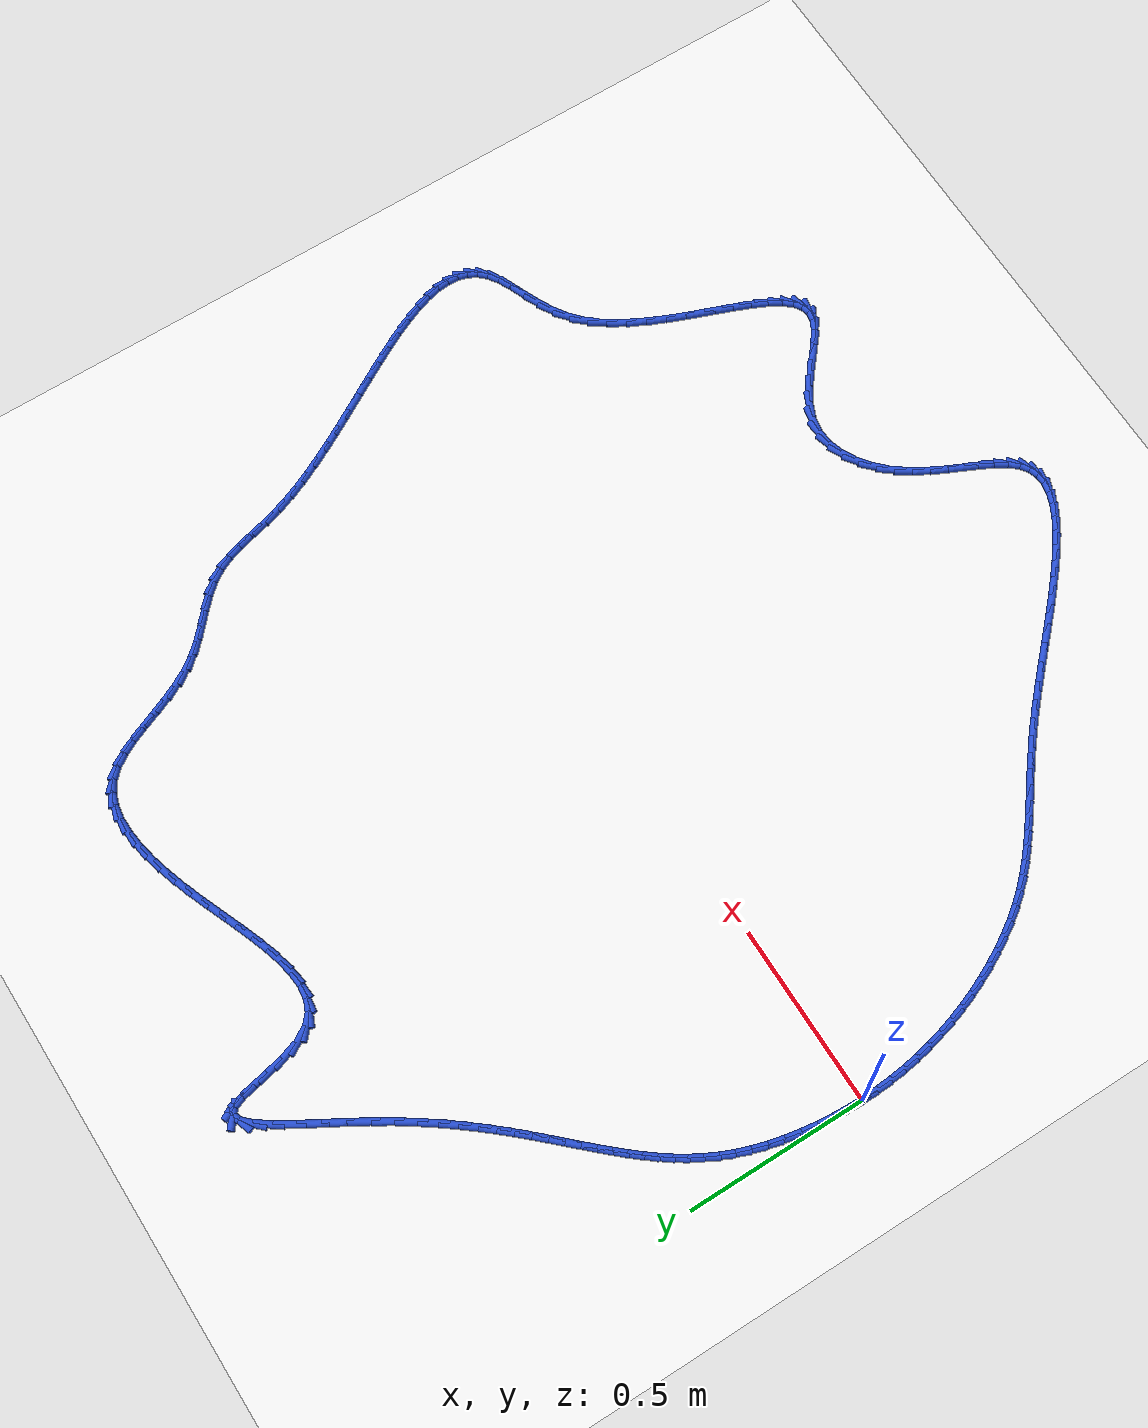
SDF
<sdf version="1.6">
 <world name="default">
  <light name="sun" type="directional">
   <pose>0 0 10 0 -0 0</pose>
   <diffuse>0.8 0.8 0.8 1</diffuse>
   <specular>0.2 0.2 0.2 1</specular>
   <attenuation>
    <range>1000</range>
    <constant>0.9</constant>
    <linear>0.01</linear>
    <quadratic>0.001</quadratic>
   </attenuation>
   <direction>-0.5 0.1 -0.9</direction>
  </light>
  <model name="ground_plane">
   <static>1</static>
   <link name="link">
    <collision name="collision">
     <geometry><plane><normal>0 0 1</normal><size>100 100</size></plane></geometry>
     <surface><friction><ode><mu>100</mu><mu2>50</mu2></ode></friction></surface>
    </collision>
    <visual name="visual">
     <cast_shadows>0</cast_shadows>
     <geometry><plane><normal>0 0 1</normal><size>100 100</size></plane></geometry>
     <material>
      <script><uri>file://media/materials/scripts/gazebo.material</uri><name>Gazebo/WhiteGlow</name></script>
     </material>
    </visual>
   </link>
  </model>
  <gravity>0 0 -9.8</gravity>
  <magnetic_field>6e-06 2.3e-05 -4.2e-05</magnetic_field>
  <atmosphere type="adiabatic"/>
  <physics name="default_physics" default="0" type="ode">
   <max_step_size>0.001</max_step_size>
   <real_time_factor>1</real_time_factor>
   <real_time_update_rate>1000</real_time_update_rate>
  </physics>
  <scene><ambient>0.4 0.4 0.4 1</ambient><background>0.7 0.7 0.7 1</background><shadows>1</shadows></scene>
  <spherical_coordinates>
   <surface_model>EARTH_WGS84</surface_model>
   <latitude_deg>0</latitude_deg>
   <longitude_deg>0</longitude_deg>
   <elevation>0</elevation>
   <heading_deg>0</heading_deg>
  </spherical_coordinates>
  <model name="line">
   <link name="link_0">
    <pose>-1.9949319973733282e-17 1.3877787807814457e-17 0.01 0 1.57 1.5492984089262198</pose>
    <collision name="collision">
     <geometry><cylinder><radius>0.01</radius><length>0.08</length></cylinder></geometry>
    </collision>
    <visual name="visual">
     <material>
      <script><name>Gazebo/Blue</name><uri>file://media/materials/scripts/gazebo.material</uri></script>
     </material>
     <geometry><cylinder><radius>0.01</radius><length>0.08</length></cylinder></geometry>
    </visual>
   </link>
   <link name="link_1">
    <pose>0.0009379973051237275 0.043625285231856235 0.01 0 1.57 1.5080627157144535</pose>
    <collision name="collision">
     <geometry><cylinder><radius>0.01</radius><length>0.08</length></cylinder></geometry>
    </collision>
    <visual name="visual">
     <material>
      <script><name>Gazebo/Blue</name><uri>file://media/materials/scripts/gazebo.material</uri></script>
     </material>
     <geometry><cylinder><radius>0.01</radius><length>0.08</length></cylinder></geometry>
    </visual>
   </link>
   <link name="link_2">
    <pose>0.003688213140414482 0.08740735055196684 0.01 0 1.57 1.466742938459368</pose>
    <collision name="collision">
     <geometry><cylinder><radius>0.01</radius><length>0.08</length></cylinder></geometry>
    </collision>
    <visual name="visual">
     <material>
      <script><name>Gazebo/Blue</name><uri>file://media/materials/scripts/gazebo.material</uri></script>
     </material>
     <geometry><cylinder><radius>0.01</radius><length>0.08</length></cylinder></geometry>
    </visual>
   </link>
   <link name="link_3">
    <pose>0.008240092487205775 0.13099497084447456 0.01 0 1.57 1.424481866338561</pose>
    <collision name="collision">
     <geometry><cylinder><radius>0.01</radius><length>0.08</length></cylinder></geometry>
    </collision>
    <visual name="visual">
     <material>
      <script><name>Gazebo/Blue</name><uri>file://media/materials/scripts/gazebo.material</uri></script>
     </material>
     <geometry><cylinder><radius>0.01</radius><length>0.08</length></cylinder></geometry>
    </visual>
   </link>
   <link name="link_4">
    <pose>0.014583080326831128 0.17403692099352203 0.01 0 1.57 1.380379664769325</pose>
    <collision name="collision">
     <geometry><cylinder><radius>0.01</radius><length>0.08</length></cylinder></geometry>
    </collision>
    <visual name="visual">
     <material>
      <script><name>Gazebo/Blue</name><uri>file://media/materials/scripts/gazebo.material</uri></script>
     </material>
     <geometry><cylinder><radius>0.01</radius><length>0.08</length></cylinder></geometry>
    </visual>
   </link>
   <link name="link_5">
    <pose>0.022706621640624085 0.216181975883252 0.01 0 1.57 1.3334424046194615</pose>
    <collision name="collision">
     <geometry><cylinder><radius>0.01</radius><length>0.08</length></cylinder></geometry>
    </collision>
    <visual name="visual">
     <material>
      <script><name>Gazebo/Blue</name><uri>file://media/materials/scripts/gazebo.material</uri></script>
     </material>
     <geometry><cylinder><radius>0.01</radius><length>0.08</length></cylinder></geometry>
    </visual>
   </link>
   <link name="link_6">
    <pose>0.03260016140991818 0.2570789103978071 0.01 0 1.57 1.2825244340216646</pose>
    <collision name="collision">
     <geometry><cylinder><radius>0.01</radius><length>0.08</length></cylinder></geometry>
    </collision>
    <visual name="visual">
     <material>
      <script><name>Gazebo/Blue</name><uri>file://media/materials/scripts/gazebo.material</uri></script>
     </material>
     <geometry><cylinder><radius>0.01</radius><length>0.08</length></cylinder></geometry>
    </visual>
   </link>
   <link name="link_7">
    <pose>0.04425314461604691 0.2963764994213299 0.01 0 1.57 1.2262796433510488</pose>
    <collision name="collision">
     <geometry><cylinder><radius>0.01</radius><length>0.08</length></cylinder></geometry>
    </collision>
    <visual name="visual">
     <material>
      <script><name>Gazebo/Blue</name><uri>file://media/materials/scripts/gazebo.material</uri></script>
     </material>
     <geometry><cylinder><radius>0.01</radius><length>0.08</length></cylinder></geometry>
    </visual>
   </link>
   <link name="link_8">
    <pose>0.057654824972781044 0.3337250938340717 0.01 0 1.57 1.165661050903397</pose>
    <collision name="collision">
     <geometry><cylinder><radius>0.01</radius><length>0.08</length></cylinder></geometry>
    </collision>
    <visual name="visual">
     <material>
      <script><name>Gazebo/Blue</name><uri>file://media/materials/scripts/gazebo.material</uri></script>
     </material>
     <geometry><cylinder><radius>0.01</radius><length>0.08</length></cylinder></geometry>
    </visual>
   </link>
   <link name="link_9">
    <pose>0.0727706078944984 0.3689715484424024 0.01 0 1.57 1.1056971633202628</pose>
    <collision name="collision">
     <geometry><cylinder><radius>0.01</radius><length>0.08</length></cylinder></geometry>
    </collision>
    <visual name="visual">
     <material>
      <script><name>Gazebo/Blue</name><uri>file://media/materials/scripts/gazebo.material</uri></script>
     </material>
     <geometry><cylinder><radius>0.01</radius><length>0.08</length></cylinder></geometry>
    </visual>
   </link>
   <link name="link_10">
    <pose>0.08951919778035933 0.4023475225493513 0.01 0 1.57 1.0484859094666872</pose>
    <collision name="collision">
     <geometry><cylinder><radius>0.01</radius><length>0.08</length></cylinder></geometry>
    </collision>
    <visual name="visual">
     <material>
      <script><name>Gazebo/Blue</name><uri>file://media/materials/scripts/gazebo.material</uri></script>
     </material>
     <geometry><cylinder><radius>0.01</radius><length>0.08</length></cylinder></geometry>
    </visual>
   </link>
   <link name="link_11">
    <pose>0.1078138793877399 0.4341293319288855 0.01 0 1.57 0.9955183735203197</pose>
    <collision name="collision">
     <geometry><cylinder><radius>0.01</radius><length>0.08</length></cylinder></geometry>
    </collision>
    <visual name="visual">
     <material>
      <script><name>Gazebo/Blue</name><uri>file://media/materials/scripts/gazebo.material</uri></script>
     </material>
     <geometry><cylinder><radius>0.01</radius><length>0.08</length></cylinder></geometry>
    </visual>
   </link>
   <link name="link_12">
    <pose>0.12756793747401624 0.46459329235497243 0.01 0 1.57 0.9480599318399198</pose>
    <collision name="collision">
     <geometry><cylinder><radius>0.01</radius><length>0.08</length></cylinder></geometry>
    </collision>
    <visual name="visual">
     <material>
      <script><name>Gazebo/Blue</name><uri>file://media/materials/scripts/gazebo.material</uri></script>
     </material>
     <geometry><cylinder><radius>0.01</radius><length>0.08</length></cylinder></geometry>
    </visual>
   </link>
   <link name="link_13">
    <pose>0.14869465679656432 0.4940157196015791 0.01 0 1.57 0.9070687154058916</pose>
    <collision name="collision">
     <geometry><cylinder><radius>0.01</radius><length>0.08</length></cylinder></geometry>
    </collision>
    <visual name="visual">
     <material>
      <script><name>Gazebo/Blue</name><uri>file://media/materials/scripts/gazebo.material</uri></script>
     </material>
     <geometry><cylinder><radius>0.01</radius><length>0.08</length></cylinder></geometry>
    </visual>
   </link>
   <link name="link_14">
    <pose>0.17110732211276017 0.522672929442673 0.01 0 1.57 0.8731673445609649</pose>
    <collision name="collision">
     <geometry><cylinder><radius>0.01</radius><length>0.08</length></cylinder></geometry>
    </collision>
    <visual name="visual">
     <material>
      <script><name>Gazebo/Blue</name><uri>file://media/materials/scripts/gazebo.material</uri></script>
     </material>
     <geometry><cylinder><radius>0.01</radius><length>0.08</length></cylinder></geometry>
    </visual>
   </link>
   <link name="link_15">
    <pose>0.19471921817997995 0.550841237652221 0.01 0 1.57 0.8466597277962639</pose>
    <collision name="collision">
     <geometry><cylinder><radius>0.01</radius><length>0.08</length></cylinder></geometry>
    </collision>
    <visual name="visual">
     <material>
      <script><name>Gazebo/Blue</name><uri>file://media/materials/scripts/gazebo.material</uri></script>
     </material>
     <geometry><cylinder><radius>0.01</radius><length>0.08</length></cylinder></geometry>
    </visual>
   </link>
   <link name="link_16">
    <pose>0.21944362975559972 0.5787969600041911 0.01 0 1.57 0.8275761211800636</pose>
    <collision name="collision">
     <geometry><cylinder><radius>0.01</radius><length>0.08</length></cylinder></geometry>
    </collision>
    <visual name="visual">
     <material>
      <script><name>Gazebo/Blue</name><uri>file://media/materials/scripts/gazebo.material</uri></script>
     </material>
     <geometry><cylinder><radius>0.01</radius><length>0.08</length></cylinder></geometry>
    </visual>
   </link>
   <link name="link_17">
    <pose>0.24519384159699553 0.60681641227255 0.01 0 1.57 0.8157292339989374</pose>
    <collision name="collision">
     <geometry><cylinder><radius>0.01</radius><length>0.08</length></cylinder></geometry>
    </collision>
    <visual name="visual">
     <material>
      <script><name>Gazebo/Blue</name><uri>file://media/materials/scripts/gazebo.material</uri></script>
     </material>
     <geometry><cylinder><radius>0.01</radius><length>0.08</length></cylinder></geometry>
    </visual>
   </link>
   <link name="link_18">
    <pose>0.27188313846154333 0.6351759102312649 0.01 0 1.57 0.8107687899891362</pose>
    <collision name="collision">
     <geometry><cylinder><radius>0.01</radius><length>0.08</length></cylinder></geometry>
    </collision>
    <visual name="visual">
     <material>
      <script><name>Gazebo/Blue</name><uri>file://media/materials/scripts/gazebo.material</uri></script>
     </material>
     <geometry><cylinder><radius>0.01</radius><length>0.08</length></cylinder></geometry>
    </visual>
   </link>
   <link name="link_19">
    <pose>0.2994248051066193 0.6641517696543034 0.01 0 1.57 0.8122278641269788</pose>
    <collision name="collision">
     <geometry><cylinder><radius>0.01</radius><length>0.08</length></cylinder></geometry>
    </collision>
    <visual name="visual">
     <material>
      <script><name>Gazebo/Blue</name><uri>file://media/materials/scripts/gazebo.material</uri></script>
     </material>
     <geometry><cylinder><radius>0.01</radius><length>0.08</length></cylinder></geometry>
    </visual>
   </link>
   <link name="link_20">
    <pose>0.3277321262895995 0.6940203063156328 0.01 0 1.57 0.8195591386262284</pose>
    <collision name="collision">
     <geometry><cylinder><radius>0.01</radius><length>0.08</length></cylinder></geometry>
    </collision>
    <visual name="visual">
     <material>
      <script><name>Gazebo/Blue</name><uri>file://media/materials/scripts/gazebo.material</uri></script>
     </material>
     <geometry><cylinder><radius>0.01</radius><length>0.08</length></cylinder></geometry>
    </visual>
   </link>
   <link name="link_21">
    <pose>0.35671838676786 0.7250578359892201 0.01 0 1.57 0.8321621756582159</pose>
    <collision name="collision">
     <geometry><cylinder><radius>0.01</radius><length>0.08</length></cylinder></geometry>
    </collision>
    <visual name="visual">
     <material>
      <script><name>Gazebo/Blue</name><uri>file://media/materials/scripts/gazebo.material</uri></script>
     </material>
     <geometry><cylinder><radius>0.01</radius><length>0.08</length></cylinder></geometry>
    </visual>
   </link>
   <link name="link_22">
    <pose>0.3862968712987769 0.7575406744490328 0.01 0 1.57 0.8494040755090081</pose>
    <collision name="collision">
     <geometry><cylinder><radius>0.01</radius><length>0.08</length></cylinder></geometry>
    </collision>
    <visual name="visual">
     <material>
      <script><name>Gazebo/Blue</name><uri>file://media/materials/scripts/gazebo.material</uri></script>
     </material>
     <geometry><cylinder><radius>0.01</radius><length>0.08</length></cylinder></geometry>
    </visual>
   </link>
   <link name="link_23">
    <pose>0.4163808646397261 0.7917451374690379 0.01 0 1.57 0.8706360021975161</pose>
    <collision name="collision">
     <geometry><cylinder><radius>0.01</radius><length>0.08</length></cylinder></geometry>
    </collision>
    <visual name="visual">
     <material>
      <script><name>Gazebo/Blue</name><uri>file://media/materials/scripts/gazebo.material</uri></script>
     </material>
     <geometry><cylinder><radius>0.01</radius><length>0.08</length></cylinder></geometry>
    </visual>
   </link>
   <link name="link_24">
    <pose>0.44688365154808396 0.8279475408232031 0.01 0 1.57 0.8952075259820951</pose>
    <collision name="collision">
     <geometry><cylinder><radius>0.01</radius><length>0.08</length></cylinder></geometry>
    </collision>
    <visual name="visual">
     <material>
      <script><name>Gazebo/Blue</name><uri>file://media/materials/scripts/gazebo.material</uri></script>
     </material>
     <geometry><cylinder><radius>0.01</radius><length>0.08</length></cylinder></geometry>
    </visual>
   </link>
   <link name="link_25">
    <pose>0.4777185167812262 0.8664242002854953 0.01 0 1.57 0.9224799410381123</pose>
    <collision name="collision">
     <geometry><cylinder><radius>0.01</radius><length>0.08</length></cylinder></geometry>
    </collision>
    <visual name="visual">
     <material>
      <script><name>Gazebo/Blue</name><uri>file://media/materials/scripts/gazebo.material</uri></script>
     </material>
     <geometry><cylinder><radius>0.01</radius><length>0.08</length></cylinder></geometry>
    </visual>
   </link>
   <link name="link_26">
    <pose>0.508798745096529 0.9074514316298817 0.01 0 1.57 0.9518389310442381</pose>
    <collision name="collision">
     <geometry><cylinder><radius>0.01</radius><length>0.08</length></cylinder></geometry>
    </collision>
    <visual name="visual">
     <material>
      <script><name>Gazebo/Blue</name><uri>file://media/materials/scripts/gazebo.material</uri></script>
     </material>
     <geometry><cylinder><radius>0.01</radius><length>0.08</length></cylinder></geometry>
    </visual>
   </link>
   <link name="link_27">
    <pose>0.5400376212513686 0.9513055506303301 0.01 0 1.57 0.9827063426339524</pose>
    <collision name="collision">
     <geometry><cylinder><radius>0.01</radius><length>0.08</length></cylinder></geometry>
    </collision>
    <visual name="visual">
     <material>
      <script><name>Gazebo/Blue</name><uri>file://media/materials/scripts/gazebo.material</uri></script>
     </material>
     <geometry><cylinder><radius>0.01</radius><length>0.08</length></cylinder></geometry>
    </visual>
   </link>
   <link name="link_28">
    <pose>0.5713484300031209 0.9982628730608071 0.01 0 1.57 1.0143931177944268</pose>
    <collision name="collision">
     <geometry><cylinder><radius>0.01</radius><length>0.08</length></cylinder></geometry>
    </collision>
    <visual name="visual">
     <material>
      <script><name>Gazebo/Blue</name><uri>file://media/materials/scripts/gazebo.material</uri></script>
     </material>
     <geometry><cylinder><radius>0.01</radius><length>0.08</length></cylinder></geometry>
    </visual>
   </link>
   <link name="link_29">
    <pose>0.6026414614797672 1.0485772397628415 0.01 0 1.57 1.0387962812588707</pose>
    <collision name="collision">
     <geometry><cylinder><radius>0.01</radius><length>0.08</length></cylinder></geometry>
    </collision>
    <visual name="visual">
     <material>
      <script><name>Gazebo/Blue</name><uri>file://media/materials/scripts/gazebo.material</uri></script>
     </material>
     <geometry><cylinder><radius>0.01</radius><length>0.08</length></cylinder></geometry>
    </visual>
   </link>
   <link name="link_30">
    <pose>0.6336645419196736 1.1012831871294024 0.01 0 1.57 1.0463994306227589</pose>
    <collision name="collision">
     <geometry><cylinder><radius>0.01</radius><length>0.08</length></cylinder></geometry>
    </collision>
    <visual name="visual">
     <material>
      <script><name>Gazebo/Blue</name><uri>file://media/materials/scripts/gazebo.material</uri></script>
     </material>
     <geometry><cylinder><radius>0.01</radius><length>0.08</length></cylinder></geometry>
    </visual>
   </link>
   <link name="link_31">
    <pose>0.6639231072688065 1.1535960930776197 0.01 0 1.57 1.0365891636039977</pose>
    <collision name="collision">
     <geometry><cylinder><radius>0.01</radius><length>0.08</length></cylinder></geometry>
    </collision>
    <visual name="visual">
     <material>
      <script><name>Gazebo/Blue</name><uri>file://media/materials/scripts/gazebo.material</uri></script>
     </material>
     <geometry><cylinder><radius>0.01</radius><length>0.08</length></cylinder></geometry>
    </visual>
   </link>
   <link name="link_32">
    <pose>0.6929028070472677 1.2025828368204818 0.01 0 1.57 1.0041290565451264</pose>
    <collision name="collision">
     <geometry><cylinder><radius>0.01</radius><length>0.08</length></cylinder></geometry>
    </collision>
    <visual name="visual">
     <material>
      <script><name>Gazebo/Blue</name><uri>file://media/materials/scripts/gazebo.material</uri></script>
     </material>
     <geometry><cylinder><radius>0.01</radius><length>0.08</length></cylinder></geometry>
    </visual>
   </link>
   <link name="link_33">
    <pose>0.7200892907751588 1.2453102975709789 0.01 0 1.57 0.932513668026764</pose>
    <collision name="collision">
     <geometry><cylinder><radius>0.01</radius><length>0.08</length></cylinder></geometry>
    </collision>
    <visual name="visual">
     <material>
      <script><name>Gazebo/Blue</name><uri>file://media/materials/scripts/gazebo.material</uri></script>
     </material>
     <geometry><cylinder><radius>0.01</radius><length>0.08</length></cylinder></geometry>
    </visual>
   </link>
   <link name="link_34">
    <pose>0.7449682079725823 1.2788453545421015 0.01 0 1.57 0.7705034878281544</pose>
    <collision name="collision">
     <geometry><cylinder><radius>0.01</radius><length>0.08</length></cylinder></geometry>
    </collision>
    <visual name="visual">
     <material>
      <script><name>Gazebo/Blue</name><uri>file://media/materials/scripts/gazebo.material</uri></script>
     </material>
     <geometry><cylinder><radius>0.01</radius><length>0.08</length></cylinder></geometry>
    </visual>
   </link>
   <link name="link_35">
    <pose>0.7670252081596396 1.3002548869468376 0.01 0 1.57 0.3270602481532942</pose>
    <collision name="collision">
     <geometry><cylinder><radius>0.01</radius><length>0.08</length></cylinder></geometry>
    </collision>
    <visual name="visual">
     <material>
      <script><name>Gazebo/Blue</name><uri>file://media/materials/scripts/gazebo.material</uri></script>
     </material>
     <geometry><cylinder><radius>0.01</radius><length>0.08</length></cylinder></geometry>
    </visual>
   </link>
   <link name="link_36">
    <pose>0.7857459408564329 1.306605773998178 0.01 0 1.57 -0.6607142820973615</pose>
    <collision name="collision">
     <geometry><cylinder><radius>0.01</radius><length>0.08</length></cylinder></geometry>
    </collision>
    <visual name="visual">
     <material>
      <script><name>Gazebo/Blue</name><uri>file://media/materials/scripts/gazebo.material</uri></script>
     </material>
     <geometry><cylinder><radius>0.01</radius><length>0.08</length></cylinder></geometry>
    </visual>
   </link>
   <link name="link_37">
    <pose>0.8006348275459527 1.2950333857793639 0.01 0 1.57 -1.1945812247315057</pose>
    <collision name="collision">
     <geometry><cylinder><radius>0.01</radius><length>0.08</length></cylinder></geometry>
    </collision>
    <visual name="visual">
     <material>
      <script><name>Gazebo/Blue</name><uri>file://media/materials/scripts/gazebo.material</uri></script>
     </material>
     <geometry><cylinder><radius>0.01</radius><length>0.08</length></cylinder></geometry>
    </visual>
   </link>
   <link name="link_38">
    <pose>0.8121063976511482 1.26599368730553 0.01 0 1.57 -1.3386323165650522</pose>
    <collision name="collision">
     <geometry><cylinder><radius>0.01</radius><length>0.08</length></cylinder></geometry>
    </collision>
    <visual name="visual">
     <material>
      <script><name>Gazebo/Blue</name><uri>file://media/materials/scripts/gazebo.material</uri></script>
     </material>
     <geometry><cylinder><radius>0.01</radius><length>0.08</length></cylinder></geometry>
    </visual>
   </link>
   <link name="link_39">
    <pose>0.8218738528034922 1.2246809434840373 0.01 0 1.57 -1.3679916434915367</pose>
    <collision name="collision">
     <geometry><cylinder><radius>0.01</radius><length>0.08</length></cylinder></geometry>
    </collision>
    <visual name="visual">
     <material>
      <script><name>Gazebo/Blue</name><uri>file://media/materials/scripts/gazebo.material</uri></script>
     </material>
     <geometry><cylinder><radius>0.01</radius><length>0.08</length></cylinder></geometry>
    </visual>
   </link>
   <link name="link_40">
    <pose>0.8317499719913123 1.176652734442328 0.01 0 1.57 -1.3353878458937123</pose>
    <collision name="collision">
     <geometry><cylinder><radius>0.01</radius><length>0.08</length></cylinder></geometry>
    </collision>
    <visual name="visual">
     <material>
      <script><name>Gazebo/Blue</name><uri>file://media/materials/scripts/gazebo.material</uri></script>
     </material>
     <geometry><cylinder><radius>0.01</radius><length>0.08</length></cylinder></geometry>
    </visual>
   </link>
   <link name="link_41">
    <pose>0.8435475342029368 1.127466640307844 0.01 0 1.57 -1.2369778965501237</pose>
    <collision name="collision">
     <geometry><cylinder><radius>0.01</radius><length>0.08</length></cylinder></geometry>
    </collision>
    <visual name="visual">
     <material>
      <script><name>Gazebo/Blue</name><uri>file://media/materials/scripts/gazebo.material</uri></script>
     </material>
     <geometry><cylinder><radius>0.01</radius><length>0.08</length></cylinder></geometry>
    </visual>
   </link>
   <link name="link_42">
    <pose>0.859079318426693 1.0826802412080279 0.01 0 1.57 -1.031243513745961</pose>
    <collision name="collision">
     <geometry><cylinder><radius>0.01</radius><length>0.08</length></cylinder></geometry>
    </collision>
    <visual name="visual">
     <material>
      <script><name>Gazebo/Blue</name><uri>file://media/materials/scripts/gazebo.material</uri></script>
     </material>
     <geometry><cylinder><radius>0.01</radius><length>0.08</length></cylinder></geometry>
    </visual>
   </link>
   <link name="link_43">
    <pose>0.8800751064530079 1.0476184183092851 0.01 0 1.57 -0.7217724448354997</pose>
    <collision name="collision">
     <geometry><cylinder><radius>0.01</radius><length>0.08</length></cylinder></geometry>
    </collision>
    <visual name="visual">
     <material>
      <script><name>Gazebo/Blue</name><uri>file://media/materials/scripts/gazebo.material</uri></script>
     </material>
     <geometry><cylinder><radius>0.01</radius><length>0.08</length></cylinder></geometry>
    </visual>
   </link>
   <link name="link_44">
    <pose>0.9069616221741095 1.0239526737875424 0.01 0 1.57 -0.3973663996892161</pose>
    <collision name="collision">
     <geometry><cylinder><radius>0.01</radius><length>0.08</length></cylinder></geometry>
    </collision>
    <visual name="visual">
     <material>
      <script><name>Gazebo/Blue</name><uri>file://media/materials/scripts/gazebo.material</uri></script>
     </material>
     <geometry><cylinder><radius>0.01</radius><length>0.08</length></cylinder></geometry>
    </visual>
   </link>
   <link name="link_45">
    <pose>0.939130255100037 1.0104517463381182 0.01 0 1.57 -0.12557861818949256</pose>
    <collision name="collision">
     <geometry><cylinder><radius>0.01</radius><length>0.08</length></cylinder></geometry>
    </collision>
    <visual name="visual">
     <material>
      <script><name>Gazebo/Blue</name><uri>file://media/materials/scripts/gazebo.material</uri></script>
     </material>
     <geometry><cylinder><radius>0.01</radius><length>0.08</length></cylinder></geometry>
    </visual>
   </link>
   <link name="link_46">
    <pose>0.9759438316589492 1.0058042924409583 0.01 0 1.57 0.07079234633715945</pose>
    <collision name="collision">
     <geometry><cylinder><radius>0.01</radius><length>0.08</length></cylinder></geometry>
    </collision>
    <visual name="visual">
     <material>
      <script><name>Gazebo/Blue</name><uri>file://media/materials/scripts/gazebo.material</uri></script>
     </material>
     <geometry><cylinder><radius>0.01</radius><length>0.08</length></cylinder></geometry>
    </visual>
   </link>
   <link name="link_47">
    <pose>1.0167651782790044 1.0086989685760086 0.01 0 1.57 0.20363390826413982</pose>
    <collision name="collision">
     <geometry><cylinder><radius>0.01</radius><length>0.08</length></cylinder></geometry>
    </collision>
    <visual name="visual">
     <material>
      <script><name>Gazebo/Blue</name><uri>file://media/materials/scripts/gazebo.material</uri></script>
     </material>
     <geometry><cylinder><radius>0.01</radius><length>0.08</length></cylinder></geometry>
    </visual>
   </link>
   <link name="link_48">
    <pose>1.0609571213883615 1.017824431223215 0.01 0 1.57 0.29081727731757046</pose>
    <collision name="collision">
     <geometry><cylinder><radius>0.01</radius><length>0.08</length></cylinder></geometry>
    </collision>
    <visual name="visual">
     <material>
      <script><name>Gazebo/Blue</name><uri>file://media/materials/scripts/gazebo.material</uri></script>
     </material>
     <geometry><cylinder><radius>0.01</radius><length>0.08</length></cylinder></geometry>
    </visual>
   </link>
   <link name="link_49">
    <pose>1.1078824874151785 1.031869336862523 0.01 0 1.57 0.3456499086569815</pose>
    <collision name="collision">
     <geometry><cylinder><radius>0.01</radius><length>0.08</length></cylinder></geometry>
    </collision>
    <visual name="visual">
     <material>
      <script><name>Gazebo/Blue</name><uri>file://media/materials/scripts/gazebo.material</uri></script>
     </material>
     <geometry><cylinder><radius>0.01</radius><length>0.08</length></cylinder></geometry>
    </visual>
   </link>
   <link name="link_50">
    <pose>1.156904102787615 1.0495223419738784 0.01 0 1.57 0.3763580443483489</pose>
    <collision name="collision">
     <geometry><cylinder><radius>0.01</radius><length>0.08</length></cylinder></geometry>
    </collision>
    <visual name="visual">
     <material>
      <script><name>Gazebo/Blue</name><uri>file://media/materials/scripts/gazebo.material</uri></script>
     </material>
     <geometry><cylinder><radius>0.01</radius><length>0.08</length></cylinder></geometry>
    </visual>
   </link>
   <link name="link_51">
    <pose>1.207384793933829 1.069472103037227 0.01 0 1.57 0.38744593252711956</pose>
    <collision name="collision">
     <geometry><cylinder><radius>0.01</radius><length>0.08</length></cylinder></geometry>
    </collision>
    <visual name="visual">
     <material>
      <script><name>Gazebo/Blue</name><uri>file://media/materials/scripts/gazebo.material</uri></script>
     </material>
     <geometry><cylinder><radius>0.01</radius><length>0.08</length></cylinder></geometry>
    </visual>
   </link>
   <link name="link_52">
    <pose>1.258687387281979 1.0904072765325146 0.01 0 1.57 0.3807460116582707</pose>
    <collision name="collision">
     <geometry><cylinder><radius>0.01</radius><length>0.08</length></cylinder></geometry>
    </collision>
    <visual name="visual">
     <material>
      <script><name>Gazebo/Blue</name><uri>file://media/materials/scripts/gazebo.material</uri></script>
     </material>
     <geometry><cylinder><radius>0.01</radius><length>0.08</length></cylinder></geometry>
    </visual>
   </link>
   <link name="link_53">
    <pose>1.310174709260223 1.1110165189396866 0.01 0 1.57 0.35631748665630925</pose>
    <collision name="collision">
     <geometry><cylinder><radius>0.01</radius><length>0.08</length></cylinder></geometry>
    </collision>
    <visual name="visual">
     <material>
      <script><name>Gazebo/Blue</name><uri>file://media/materials/scripts/gazebo.material</uri></script>
     </material>
     <geometry><cylinder><radius>0.01</radius><length>0.08</length></cylinder></geometry>
    </visual>
   </link>
   <link name="link_54">
    <pose>1.3612157297149343 1.1300142115183733 0.01 0 1.57 0.31801333983110247</pose>
    <collision name="collision">
     <geometry><cylinder><radius>0.01</radius><length>0.08</length></cylinder></geometry>
    </collision>
    <visual name="visual">
     <material>
      <script><name>Gazebo/Blue</name><uri>file://media/materials/scripts/gazebo.material</uri></script>
     </material>
     <geometry><cylinder><radius>0.01</radius><length>0.08</length></cylinder></geometry>
    </visual>
   </link>
   <link name="link_55">
    <pose>1.4112693114642254 1.1464911508743354 0.01 0 1.57 0.267779421817082</pose>
    <collision name="collision">
     <geometry><cylinder><radius>0.01</radius><length>0.08</length></cylinder></geometry>
    </collision>
    <visual name="visual">
     <material>
      <script><name>Gazebo/Blue</name><uri>file://media/materials/scripts/gazebo.material</uri></script>
     </material>
     <geometry><cylinder><radius>0.01</radius><length>0.08</length></cylinder></geometry>
    </visual>
   </link>
   <link name="link_56">
    <pose>1.459862492969172 1.1598236104169863 0.01 0 1.57 0.2023166972554978</pose>
    <collision name="collision">
     <geometry><cylinder><radius>0.01</radius><length>0.08</length></cylinder></geometry>
    </collision>
    <visual name="visual">
     <material>
      <script><name>Gazebo/Blue</name><uri>file://media/materials/scripts/gazebo.material</uri></script>
     </material>
     <geometry><cylinder><radius>0.01</radius><length>0.08</length></cylinder></geometry>
    </visual>
   </link>
   <link name="link_57">
    <pose>1.506524008256687 1.1693949635212724 0.01 0 1.57 0.11681295212326884</pose>
    <collision name="collision">
     <geometry><cylinder><radius>0.01</radius><length>0.08</length></cylinder></geometry>
    </collision>
    <visual name="visual">
     <material>
      <script><name>Gazebo/Blue</name><uri>file://media/materials/scripts/gazebo.material</uri></script>
     </material>
     <geometry><cylinder><radius>0.01</radius><length>0.08</length></cylinder></geometry>
    </visual>
   </link>
   <link name="link_58">
    <pose>1.5507825913536817 1.1745885835621388 0.01 0 1.57 0.0048148308334593415</pose>
    <collision name="collision">
     <geometry><cylinder><radius>0.01</radius><length>0.08</length></cylinder></geometry>
    </collision>
    <visual name="visual">
     <material>
      <script><name>Gazebo/Blue</name><uri>file://media/materials/scripts/gazebo.material</uri></script>
     </material>
     <geometry><cylinder><radius>0.01</radius><length>0.08</length></cylinder></geometry>
    </visual>
   </link>
   <link name="link_59">
    <pose>1.5921669762870687 1.174787843914533 0.01 0 1.57 -0.1413197701401831</pose>
    <collision name="collision">
     <geometry><cylinder><radius>0.01</radius><length>0.08</length></cylinder></geometry>
    </collision>
    <visual name="visual">
     <material>
      <script><name>Gazebo/Blue</name><uri>file://media/materials/scripts/gazebo.material</uri></script>
     </material>
     <geometry><cylinder><radius>0.01</radius><length>0.08</length></cylinder></geometry>
    </visual>
   </link>
   <link name="link_60">
    <pose>1.6302058970837594 1.1693761179534001 0.01 0 1.57 -0.32783788104168265</pose>
    <collision name="collision">
     <geometry><cylinder><radius>0.01</radius><length>0.08</length></cylinder></geometry>
    </collision>
    <visual name="visual">
     <material>
      <script><name>Gazebo/Blue</name><uri>file://media/materials/scripts/gazebo.material</uri></script>
     </material>
     <geometry><cylinder><radius>0.01</radius><length>0.08</length></cylinder></geometry>
    </visual>
   </link>
   <link name="link_61">
    <pose>1.6644280877706663 1.1577367790536865 0.01 0 1.57 -0.5531671321172079</pose>
    <collision name="collision">
     <geometry><cylinder><radius>0.01</radius><length>0.08</length></cylinder></geometry>
    </collision>
    <visual name="visual">
     <material>
      <script><name>Gazebo/Blue</name><uri>file://media/materials/scripts/gazebo.material</uri></script>
     </material>
     <geometry><cylinder><radius>0.01</radius><length>0.08</length></cylinder></geometry>
    </visual>
   </link>
   <link name="link_62">
    <pose>1.694362319674856 1.1392532482664355 0.01 0 1.57 -0.7871714292794221</pose>
    <collision name="collision">
     <geometry><cylinder><radius>0.01</radius><length>0.08</length></cylinder></geometry>
    </collision>
    <visual name="visual">
     <material>
      <script><name>Gazebo/Blue</name><uri>file://media/materials/scripts/gazebo.material</uri></script>
     </material>
     <geometry><cylinder><radius>0.01</radius><length>0.08</length></cylinder></geometry>
    </visual>
   </link>
   <link name="link_63">
    <pose>1.7198353026389053 1.1136897639814174 0.01 0 1.57 -0.96536039960385</pose>
    <collision name="collision">
     <geometry><cylinder><radius>0.01</radius><length>0.08</length></cylinder></geometry>
    </collision>
    <visual name="visual">
     <material>
      <script><name>Gazebo/Blue</name><uri>file://media/materials/scripts/gazebo.material</uri></script>
     </material>
     <geometry><cylinder><radius>0.01</radius><length>0.08</length></cylinder></geometry>
    </visual>
   </link>
   <link name="link_64">
    <pose>1.7416918430098158 1.082111869324773 0.01 0 1.57 -1.0814972308968964</pose>
    <collision name="collision">
     <geometry><cylinder><radius>0.01</radius><length>0.08</length></cylinder></geometry>
    </collision>
    <visual name="visual">
     <material>
      <script><name>Gazebo/Blue</name><uri>file://media/materials/scripts/gazebo.material</uri></script>
     </material>
     <geometry><cylinder><radius>0.01</radius><length>0.08</length></cylinder></geometry>
    </visual>
   </link>
   <link name="link_65">
    <pose>1.7609940276946041 1.0458628298395667 0.01 0 1.57 -1.147936045333331</pose>
    <collision name="collision">
     <geometry><cylinder><radius>0.01</radius><length>0.08</length></cylinder></geometry>
    </collision>
    <visual name="visual">
     <material>
      <script><name>Gazebo/Blue</name><uri>file://media/materials/scripts/gazebo.material</uri></script>
     </material>
     <geometry><cylinder><radius>0.01</radius><length>0.08</length></cylinder></geometry>
    </visual>
   </link>
   <link name="link_66">
    <pose>1.778803943600286 1.0062859110688636 0.01 0 1.57 -1.174726009654299</pose>
    <collision name="collision">
     <geometry><cylinder><radius>0.01</radius><length>0.08</length></cylinder></geometry>
    </collision>
    <visual name="visual">
     <material>
      <script><name>Gazebo/Blue</name><uri>file://media/materials/scripts/gazebo.material</uri></script>
     </material>
     <geometry><cylinder><radius>0.01</radius><length>0.08</length></cylinder></geometry>
    </visual>
   </link>
   <link name="link_67">
    <pose>1.79618367763388 0.9647243785557277 0.01 0 1.57 -1.167413084196343</pose>
    <collision name="collision">
     <geometry><cylinder><radius>0.01</radius><length>0.08</length></cylinder></geometry>
    </collision>
    <visual name="visual">
     <material>
      <script><name>Gazebo/Blue</name><uri>file://media/materials/scripts/gazebo.material</uri></script>
     </material>
     <geometry><cylinder><radius>0.01</radius><length>0.08</length></cylinder></geometry>
    </visual>
   </link>
   <link name="link_68">
    <pose>1.8141953167024012 0.9225214978432243 0.01 0 1.57 -1.1274920412151415</pose>
    <collision name="collision">
     <geometry><cylinder><radius>0.01</radius><length>0.08</length></cylinder></geometry>
    </collision>
    <visual name="visual">
     <material>
      <script><name>Gazebo/Blue</name><uri>file://media/materials/scripts/gazebo.material</uri></script>
     </material>
     <geometry><cylinder><radius>0.01</radius><length>0.08</length></cylinder></geometry>
    </visual>
   </link>
   <link name="link_69">
    <pose>1.8339009477128678 0.8810205344744182 0.01 0 1.57 -1.0532652184335236</pose>
    <collision name="collision">
     <geometry><cylinder><radius>0.01</radius><length>0.08</length></cylinder></geometry>
    </collision>
    <visual name="visual">
     <material>
      <script><name>Gazebo/Blue</name><uri>file://media/materials/scripts/gazebo.material</uri></script>
     </material>
     <geometry><cylinder><radius>0.01</radius><length>0.08</length></cylinder></geometry>
    </visual>
   </link>
   <link name="link_70">
    <pose>1.8563626575722953 0.8415647539923743 0.01 0 1.57 -0.9419493873683122</pose>
    <collision name="collision">
     <geometry><cylinder><radius>0.01</radius><length>0.08</length></cylinder></geometry>
    </collision>
    <visual name="visual">
     <material>
      <script><name>Gazebo/Blue</name><uri>file://media/materials/scripts/gazebo.material</uri></script>
     </material>
     <geometry><cylinder><radius>0.01</radius><length>0.08</length></cylinder></geometry>
    </visual>
   </link>
   <link name="link_71">
    <pose>1.8826147861111961 0.8054719207904373 0.01 0 1.57 -0.8261549318681671</pose>
    <collision name="collision">
     <geometry><cylinder><radius>0.01</radius><length>0.08</length></cylinder></geometry>
    </collision>
    <visual name="visual">
     <material>
      <script><name>Gazebo/Blue</name><uri>file://media/materials/scripts/gazebo.material</uri></script>
     </material>
     <geometry><cylinder><radius>0.01</radius><length>0.08</length></cylinder></geometry>
    </visual>
   </link>
   <link name="link_72">
    <pose>1.9125404688837726 0.7730017767131067 0.01 0 1.57 -0.7540653475367733</pose>
    <collision name="collision">
     <geometry><cylinder><radius>0.01</radius><length>0.08</length></cylinder></geometry>
    </collision>
    <visual name="visual">
     <material>
      <script><name>Gazebo/Blue</name><uri>file://media/materials/scripts/gazebo.material</uri></script>
     </material>
     <geometry><cylinder><radius>0.01</radius><length>0.08</length></cylinder></geometry>
    </visual>
   </link>
   <link name="link_73">
    <pose>1.9444840148615217 0.7429997939945471 0.01 0 1.57 -0.7295182722505341</pose>
    <collision name="collision">
     <geometry><cylinder><radius>0.01</radius><length>0.08</length></cylinder></geometry>
    </collision>
    <visual name="visual">
     <material>
      <script><name>Gazebo/Blue</name><uri>file://media/materials/scripts/gazebo.material</uri></script>
     </material>
     <geometry><cylinder><radius>0.01</radius><length>0.08</length></cylinder></geometry>
    </visual>
   </link>
   <link name="link_74">
    <pose>1.9766824089042447 0.71421280787413 0.01 0 1.57 -0.7540707573706579</pose>
    <collision name="collision">
     <geometry><cylinder><radius>0.01</radius><length>0.08</length></cylinder></geometry>
    </collision>
    <visual name="visual">
     <material>
      <script><name>Gazebo/Blue</name><uri>file://media/materials/scripts/gazebo.material</uri></script>
     </material>
     <geometry><cylinder><radius>0.01</radius><length>0.08</length></cylinder></geometry>
    </visual>
   </link>
   <link name="link_75">
    <pose>2.007372635871744 0.6853876535912277 0.01 0 1.57 -0.8322469300334641</pose>
    <collision name="collision">
     <geometry><cylinder><radius>0.01</radius><length>0.08</length></cylinder></geometry>
    </collision>
    <visual name="visual">
     <material>
      <script><name>Gazebo/Blue</name><uri>file://media/materials/scripts/gazebo.material</uri></script>
     </material>
     <geometry><cylinder><radius>0.01</radius><length>0.08</length></cylinder></geometry>
    </visual>
   </link>
   <link name="link_76">
    <pose>2.034791680623822 0.6552711663852134 0.01 0 1.57 -0.9694471010013458</pose>
    <collision name="collision">
     <geometry><cylinder><radius>0.01</radius><length>0.08</length></cylinder></geometry>
    </collision>
    <visual name="visual">
     <material>
      <script><name>Gazebo/Blue</name><uri>file://media/materials/scripts/gazebo.material</uri></script>
     </material>
     <geometry><cylinder><radius>0.01</radius><length>0.08</length></cylinder></geometry>
    </visual>
   </link>
   <link name="link_77">
    <pose>2.057195049206189 0.6226188760591167 0.01 0 1.57 -1.1292939003531757</pose>
    <collision name="collision">
     <geometry><cylinder><radius>0.01</radius><length>0.08</length></cylinder></geometry>
    </collision>
    <visual name="visual">
     <material>
      <script><name>Gazebo/Blue</name><uri>file://media/materials/scripts/gazebo.material</uri></script>
     </material>
     <geometry><cylinder><radius>0.01</radius><length>0.08</length></cylinder></geometry>
    </visual>
   </link>
   <link name="link_78">
    <pose>2.0741276368333073 0.5867916017459214 0.01 0 1.57 -1.2436740747268564</pose>
    <collision name="collision">
     <geometry><cylinder><radius>0.01</radius><length>0.08</length></cylinder></geometry>
    </collision>
    <visual name="visual">
     <material>
      <script><name>Gazebo/Blue</name><uri>file://media/materials/scripts/gazebo.material</uri></script>
     </material>
     <geometry><cylinder><radius>0.01</radius><length>0.08</length></cylinder></geometry>
    </visual>
   </link>
   <link name="link_79">
    <pose>2.0872426526098837 0.5481398869635236 0.01 0 1.57 -1.3055801552807036</pose>
    <collision name="collision">
     <geometry><cylinder><radius>0.01</radius><length>0.08</length></cylinder></geometry>
    </collision>
    <visual name="visual">
     <material>
      <script><name>Gazebo/Blue</name><uri>file://media/materials/scripts/gazebo.material</uri></script>
     </material>
     <geometry><cylinder><radius>0.01</radius><length>0.08</length></cylinder></geometry>
    </visual>
   </link>
   <link name="link_80">
    <pose>2.0983881302694583 0.5071057334736936 0.01 0 1.57 -1.319687801918643</pose>
    <collision name="collision">
     <geometry><cylinder><radius>0.01</radius><length>0.08</length></cylinder></geometry>
    </collision>
    <visual name="visual">
     <material>
      <script><name>Gazebo/Blue</name><uri>file://media/materials/scripts/gazebo.material</uri></script>
     </material>
     <geometry><cylinder><radius>0.01</radius><length>0.08</length></cylinder></geometry>
    </visual>
   </link>
   <link name="link_81">
    <pose>2.1094121035455724 0.4641311430382011 0.01 0 1.57 -1.2915837938700183</pose>
    <collision name="collision">
     <geometry><cylinder><radius>0.01</radius><length>0.08</length></cylinder></geometry>
    </collision>
    <visual name="visual">
     <material>
      <script><name>Gazebo/Blue</name><uri>file://media/materials/scripts/gazebo.material</uri></script>
     </material>
     <geometry><cylinder><radius>0.01</radius><length>0.08</length></cylinder></geometry>
    </visual>
   </link>
   <link name="link_82">
    <pose>2.122162606171765 0.41965811741881576 0.01 0 1.57 -1.2324761376864126</pose>
    <collision name="collision">
     <geometry><cylinder><radius>0.01</radius><length>0.08</length></cylinder></geometry>
    </collision>
    <visual name="visual">
     <material>
      <script><name>Gazebo/Blue</name><uri>file://media/materials/scripts/gazebo.material</uri></script>
     </material>
     <geometry><cylinder><radius>0.01</radius><length>0.08</length></cylinder></geometry>
    </visual>
   </link>
   <link name="link_83">
    <pose>2.1381921397637194 0.3740999960352579 0.01 0 1.57 -1.176639903611295</pose>
    <collision name="collision">
     <geometry><cylinder><radius>0.01</radius><length>0.08</length></cylinder></geometry>
    </collision>
    <visual name="visual">
     <material>
      <script><name>Gazebo/Blue</name><uri>file://media/materials/scripts/gazebo.material</uri></script>
     </material>
     <geometry><cylinder><radius>0.01</radius><length>0.08</length></cylinder></geometry>
    </visual>
   </link>
   <link name="link_84">
    <pose>2.1574834820642965 0.327717877789721 0.01 0 1.57 -1.1326743729915973</pose>
    <collision name="collision">
     <geometry><cylinder><radius>0.01</radius><length>0.08</length></cylinder></geometry>
    </collision>
    <visual name="visual">
     <material>
      <script><name>Gazebo/Blue</name><uri>file://media/materials/scripts/gazebo.material</uri></script>
     </material>
     <geometry><cylinder><radius>0.01</radius><length>0.08</length></cylinder></geometry>
    </visual>
   </link>
   <link name="link_85">
    <pose>2.1795002597391573 0.2807225114368136 0.01 0 1.57 -1.0986353999968523</pose>
    <collision name="collision">
     <geometry><cylinder><radius>0.01</radius><length>0.08</length></cylinder></geometry>
    </collision>
    <visual name="visual">
     <material>
      <script><name>Gazebo/Blue</name><uri>file://media/materials/scripts/gazebo.material</uri></script>
     </material>
     <geometry><cylinder><radius>0.01</radius><length>0.08</length></cylinder></geometry>
    </visual>
   </link>
   <link name="link_86">
    <pose>2.203705768825365 0.23332461366495097 0.01 0 1.57 -1.0730784290778024</pose>
    <collision name="collision">
     <geometry><cylinder><radius>0.01</radius><length>0.08</length></cylinder></geometry>
    </collision>
    <visual name="visual">
     <material>
      <script><name>Gazebo/Blue</name><uri>file://media/materials/scripts/gazebo.material</uri></script>
     </material>
     <geometry><cylinder><radius>0.01</radius><length>0.08</length></cylinder></geometry>
    </visual>
   </link>
   <link name="link_87">
    <pose>2.229563305359982 0.18573490116254715 0.01 0 1.57 -1.0549916950004077</pose>
    <collision name="collision">
     <geometry><cylinder><radius>0.01</radius><length>0.08</length></cylinder></geometry>
    </collision>
    <visual name="visual">
     <material>
      <script><name>Gazebo/Blue</name><uri>file://media/materials/scripts/gazebo.material</uri></script>
     </material>
     <geometry><cylinder><radius>0.01</radius><length>0.08</length></cylinder></geometry>
    </visual>
   </link>
   <link name="link_88">
    <pose>2.2565361653800715 0.13816409061801746 0.01 0 1.57 -1.0437345385882713</pose>
    <collision name="collision">
     <geometry><cylinder><radius>0.01</radius><length>0.08</length></cylinder></geometry>
    </collision>
    <visual name="visual">
     <material>
      <script><name>Gazebo/Blue</name><uri>file://media/materials/scripts/gazebo.material</uri></script>
     </material>
     <geometry><cylinder><radius>0.01</radius><length>0.08</length></cylinder></geometry>
    </visual>
   </link>
   <link name="link_89">
    <pose>2.2840876449226966 0.0908228987197769 0.01 0 1.57 -1.0389985104450379</pose>
    <collision name="collision">
     <geometry><cylinder><radius>0.01</radius><length>0.08</length></cylinder></geometry>
    </collision>
    <visual name="visual">
     <material>
      <script><name>Gazebo/Blue</name><uri>file://media/materials/scripts/gazebo.material</uri></script>
     </material>
     <geometry><cylinder><radius>0.01</radius><length>0.08</length></cylinder></geometry>
    </visual>
   </link>
   <link name="link_90">
    <pose>2.311681040024919 0.043922042156240904 0.01 0 1.57 -1.0407953708663125</pose>
    <collision name="collision">
     <geometry><cylinder><radius>0.01</radius><length>0.08</length></cylinder></geometry>
    </collision>
    <visual name="visual">
     <material>
      <script><name>Gazebo/Blue</name><uri>file://media/materials/scripts/gazebo.material</uri></script>
     </material>
     <geometry><cylinder><radius>0.01</radius><length>0.08</length></cylinder></geometry>
    </visual>
   </link>
   <link name="link_91">
    <pose>2.338779646723803 -0.0023277623841766962 0.01 0 1.57 -1.0494755944911212</pose>
    <collision name="collision">
     <geometry><cylinder><radius>0.01</radius><length>0.08</length></cylinder></geometry>
    </collision>
    <visual name="visual">
     <material>
      <script><name>Gazebo/Blue</name><uri>file://media/materials/scripts/gazebo.material</uri></script>
     </material>
     <geometry><cylinder><radius>0.01</radius><length>0.08</length></cylinder></geometry>
    </visual>
   </link>
   <link name="link_92">
    <pose>2.36484676105641 -0.047715798213060476 0.01 0 1.57 -1.0657837930131375</pose>
    <collision name="collision">
     <geometry><cylinder><radius>0.01</radius><length>0.08</length></cylinder></geometry>
    </collision>
    <visual name="visual">
     <material>
      <script><name>Gazebo/Blue</name><uri>file://media/materials/scripts/gazebo.material</uri></script>
     </material>
     <geometry><cylinder><radius>0.01</radius><length>0.08</length></cylinder></geometry>
    </visual>
   </link>
   <link name="link_93">
    <pose>2.3893456790598036 -0.09203134864199504 0.01 0 1.57 -1.0909625241512648</pose>
    <collision name="collision">
     <geometry><cylinder><radius>0.01</radius><length>0.08</length></cylinder></geometry>
    </collision>
    <visual name="visual">
     <material>
      <script><name>Gazebo/Blue</name><uri>file://media/materials/scripts/gazebo.material</uri></script>
     </material>
     <geometry><cylinder><radius>0.01</radius><length>0.08</length></cylinder></geometry>
    </visual>
   </link>
   <link name="link_94">
    <pose>2.4117396967710465 -0.13506369698256643 0.01 0 1.57 -1.1269226356869482</pose>
    <collision name="collision">
     <geometry><cylinder><radius>0.01</radius><length>0.08</length></cylinder></geometry>
    </collision>
    <visual name="visual">
     <material>
      <script><name>Gazebo/Blue</name><uri>file://media/materials/scripts/gazebo.material</uri></script>
     </material>
     <geometry><cylinder><radius>0.01</radius><length>0.08</length></cylinder></geometry>
    </visual>
   </link>
   <link name="link_95">
    <pose>2.431492110227202 -0.17660212654635923 0.01 0 1.57 -1.1765039048191126</pose>
    <collision name="collision">
     <geometry><cylinder><radius>0.01</radius><length>0.08</length></cylinder></geometry>
    </collision>
    <visual name="visual">
     <material>
      <script><name>Gazebo/Blue</name><uri>file://media/materials/scripts/gazebo.material</uri></script>
     </material>
     <geometry><cylinder><radius>0.01</radius><length>0.08</length></cylinder></geometry>
    </visual>
   </link>
   <link name="link_96">
    <pose>2.448066215465332 -0.21643592064495865 0.01 0 1.57 -1.2438423264868461</pose>
    <collision name="collision">
     <geometry><cylinder><radius>0.01</radius><length>0.08</length></cylinder></geometry>
    </collision>
    <visual name="visual">
     <material>
      <script><name>Gazebo/Blue</name><uri>file://media/materials/scripts/gazebo.material</uri></script>
     </material>
     <geometry><cylinder><radius>0.01</radius><length>0.08</length></cylinder></geometry>
    </visual>
   </link>
   <link name="link_97">
    <pose>2.4609253085225 -0.25435436258994953 0.01 0 1.57 -1.334796823856299</pose>
    <collision name="collision">
     <geometry><cylinder><radius>0.01</radius><length>0.08</length></cylinder></geometry>
    </collision>
    <visual name="visual">
     <material>
      <script><name>Gazebo/Blue</name><uri>file://media/materials/scripts/gazebo.material</uri></script>
     </material>
     <geometry><cylinder><radius>0.01</radius><length>0.08</length></cylinder></geometry>
    </visual>
   </link>
   <link name="link_98">
    <pose>2.469532685435768 -0.29014673569291644 0.01 0 1.57 -1.4571382424291024</pose>
    <collision name="collision">
     <geometry><cylinder><radius>0.01</radius><length>0.08</length></cylinder></geometry>
    </collision>
    <visual name="visual">
     <material>
      <script><name>Gazebo/Blue</name><uri>file://media/materials/scripts/gazebo.material</uri></script>
     </material>
     <geometry><cylinder><radius>0.01</radius><length>0.08</length></cylinder></geometry>
    </visual>
   </link>
   <link name="link_99">
    <pose>2.4733516422421995 -0.3236023232654459 0.01 0 1.57 1.5221043186005847</pose>
    <collision name="collision">
     <geometry><cylinder><radius>0.01</radius><length>0.08</length></cylinder></geometry>
    </collision>
    <visual name="visual">
     <material>
      <script><name>Gazebo/Blue</name><uri>file://media/materials/scripts/gazebo.material</uri></script>
     </material>
     <geometry><cylinder><radius>0.01</radius><length>0.08</length></cylinder></geometry>
    </visual>
   </link>
   <link name="link_100">
    <pose>2.4718454749788576 -0.3545104086191223 0.01 0 1.57 1.3147974986627495</pose>
    <collision name="collision">
     <geometry><cylinder><radius>0.01</radius><length>0.08</length></cylinder></geometry>
    </collision>
    <visual name="visual">
     <material>
      <script><name>Gazebo/Blue</name><uri>file://media/materials/scripts/gazebo.material</uri></script>
     </material>
     <geometry><cylinder><radius>0.01</radius><length>0.08</length></cylinder></geometry>
    </visual>
   </link>
   <link name="link_101">
    <pose>2.464477479682805 -0.3826602750655307 0.01 0 1.57 1.0704867986627695</pose>
    <collision name="collision">
     <geometry><cylinder><radius>0.01</radius><length>0.08</length></cylinder></geometry>
    </collision>
    <visual name="visual">
     <material>
      <script><name>Gazebo/Blue</name><uri>file://media/materials/scripts/gazebo.material</uri></script>
     </material>
     <geometry><cylinder><radius>0.01</radius><length>0.08</length></cylinder></geometry>
    </visual>
   </link>
   <link name="link_102">
    <pose>2.4507109523911037 -0.4078412059162561 0.01 0 1.57 0.8158202208240376</pose>
    <collision name="collision">
     <geometry><cylinder><radius>0.01</radius><length>0.08</length></cylinder></geometry>
    </collision>
    <visual name="visual">
     <material>
      <script><name>Gazebo/Blue</name><uri>file://media/materials/scripts/gazebo.material</uri></script>
     </material>
     <geometry><cylinder><radius>0.01</radius><length>0.08</length></cylinder></geometry>
    </visual>
   </link>
   <link name="link_103">
    <pose>2.430009189140817 -0.42984248448288365 0.01 0 1.57 0.5879480357711722</pose>
    <collision name="collision">
     <geometry><cylinder><radius>0.01</radius><length>0.08</length></cylinder></geometry>
    </collision>
    <visual name="visual">
     <material>
      <script><name>Gazebo/Blue</name><uri>file://media/materials/scripts/gazebo.material</uri></script>
     </material>
     <geometry><cylinder><radius>0.01</radius><length>0.08</length></cylinder></geometry>
    </visual>
   </link>
   <link name="link_104">
    <pose>2.401951827123282 -0.44854518109033703 0.01 0 1.57 0.4458094744465332</pose>
    <collision name="collision">
     <geometry><cylinder><radius>0.01</radius><length>0.08</length></cylinder></geometry>
    </collision>
    <visual name="visual">
     <material>
      <script><name>Gazebo/Blue</name><uri>file://media/materials/scripts/gazebo.material</uri></script>
     </material>
     <geometry><cylinder><radius>0.01</radius><length>0.08</length></cylinder></geometry>
    </visual>
   </link>
   <link name="link_105">
    <pose>2.367570503177247 -0.4649759169379147 0.01 0 1.57 0.3913463664327163</pose>
    <collision name="collision">
     <geometry><cylinder><radius>0.01</radius><length>0.08</length></cylinder></geometry>
    </collision>
    <visual name="visual">
     <material>
      <script><name>Gazebo/Blue</name><uri>file://media/materials/scripts/gazebo.material</uri></script>
     </material>
     <geometry><cylinder><radius>0.01</radius><length>0.08</length></cylinder></geometry>
    </visual>
   </link>
   <link name="link_106">
    <pose>2.3288831643679657 -0.48093945979292274 0.01 0 1.57 0.39999568893749193</pose>
    <collision name="collision">
     <geometry><cylinder><radius>0.01</radius><length>0.08</length></cylinder></geometry>
    </collision>
    <visual name="visual">
     <material>
      <script><name>Gazebo/Blue</name><uri>file://media/materials/scripts/gazebo.material</uri></script>
     </material>
     <geometry><cylinder><radius>0.01</radius><length>0.08</length></cylinder></geometry>
    </visual>
   </link>
   <link name="link_107">
    <pose>2.2879265722632307 -0.49825542106940623 0.01 0 1.57 0.46157597236085</pose>
    <collision name="collision">
     <geometry><cylinder><radius>0.01</radius><length>0.08</length></cylinder></geometry>
    </collision>
    <visual name="visual">
     <material>
      <script><name>Gazebo/Blue</name><uri>file://media/materials/scripts/gazebo.material</uri></script>
     </material>
     <geometry><cylinder><radius>0.01</radius><length>0.08</length></cylinder></geometry>
    </visual>
   </link>
   <link name="link_108">
    <pose>2.246737488430834 -0.5187434121814105 0.01 0 1.57 0.574221441793723</pose>
    <collision name="collision">
     <geometry><cylinder><radius>0.01</radius><length>0.08</length></cylinder></geometry>
    </collision>
    <visual name="visual">
     <material>
      <script><name>Gazebo/Blue</name><uri>file://media/materials/scripts/gazebo.material</uri></script>
     </material>
     <geometry><cylinder><radius>0.01</radius><length>0.08</length></cylinder></geometry>
    </visual>
   </link>
   <link name="link_109">
    <pose>2.207352674438567 -0.5442230445429811 0.01 0 1.57 0.7295994892352478</pose>
    <collision name="collision">
     <geometry><cylinder><radius>0.01</radius><length>0.08</length></cylinder></geometry>
    </collision>
    <visual name="visual">
     <material>
      <script><name>Gazebo/Blue</name><uri>file://media/materials/scripts/gazebo.material</uri></script>
     </material>
     <geometry><cylinder><radius>0.01</radius><length>0.08</length></cylinder></geometry>
    </visual>
   </link>
   <link name="link_110">
    <pose>2.171568883334009 -0.5762207859086198 0.01 0 1.57 0.8723531948802867</pose>
    <collision name="collision">
     <geometry><cylinder><radius>0.01</radius><length>0.08</length></cylinder></geometry>
    </collision>
    <visual name="visual">
     <material>
      <script><name>Gazebo/Blue</name><uri>file://media/materials/scripts/gazebo.material</uri></script>
     </material>
     <geometry><cylinder><radius>0.01</radius><length>0.08</length></cylinder></geometry>
    </visual>
   </link>
   <link name="link_111">
    <pose>2.1395858741298652 -0.6143125537972107 0.01 0 1.57 0.982940385228043</pose>
    <collision name="collision">
     <geometry><cylinder><radius>0.01</radius><length>0.08</length></cylinder></geometry>
    </collision>
    <visual name="visual">
     <material>
      <script><name>Gazebo/Blue</name><uri>file://media/materials/scripts/gazebo.material</uri></script>
     </material>
     <geometry><cylinder><radius>0.01</radius><length>0.08</length></cylinder></geometry>
    </visual>
   </link>
   <link name="link_112">
    <pose>2.1109514012491224 -0.6572779147843489 0.01 0 1.57 1.0662874942307612</pose>
    <collision name="collision">
     <geometry><cylinder><radius>0.01</radius><length>0.08</length></cylinder></geometry>
    </collision>
    <visual name="visual">
     <material>
      <script><name>Gazebo/Blue</name><uri>file://media/materials/scripts/gazebo.material</uri></script>
     </material>
     <geometry><cylinder><radius>0.01</radius><length>0.08</length></cylinder></geometry>
    </visual>
   </link>
   <link name="link_113">
    <pose>2.085211287310953 -0.7038940759625648 0.01 0 1.57 1.1272822400929683</pose>
    <collision name="collision">
     <geometry><cylinder><radius>0.01</radius><length>0.08</length></cylinder></geometry>
    </collision>
    <visual name="visual">
     <material>
      <script><name>Gazebo/Blue</name><uri>file://media/materials/scripts/gazebo.material</uri></script>
     </material>
     <geometry><cylinder><radius>0.01</radius><length>0.08</length></cylinder></geometry>
    </visual>
   </link>
   <link name="link_114">
    <pose>2.0619113549345296 -0.7529382444243866 0.01 0 1.57 1.1696348525480413</pose>
    <collision name="collision">
     <geometry><cylinder><radius>0.01</radius><length>0.08</length></cylinder></geometry>
    </collision>
    <visual name="visual">
     <material>
      <script><name>Gazebo/Blue</name><uri>file://media/materials/scripts/gazebo.material</uri></script>
     </material>
     <geometry><cylinder><radius>0.01</radius><length>0.08</length></cylinder></geometry>
    </visual>
   </link>
   <link name="link_115">
    <pose>2.0405974267390268 -0.8031876272623425 0.01 0 1.57 1.195632098956455</pose>
    <collision name="collision">
     <geometry><cylinder><radius>0.01</radius><length>0.08</length></cylinder></geometry>
    </collision>
    <visual name="visual">
     <material>
      <script><name>Gazebo/Blue</name><uri>file://media/materials/scripts/gazebo.material</uri></script>
     </material>
     <geometry><cylinder><radius>0.01</radius><length>0.08</length></cylinder></geometry>
    </visual>
   </link>
   <link name="link_116">
    <pose>2.020815325343617 -0.8534194315689616 0.01 0 1.57 1.206085880422435</pose>
    <collision name="collision">
     <geometry><cylinder><radius>0.01</radius><length>0.08</length></cylinder></geometry>
    </collision>
    <visual name="visual">
     <material>
      <script><name>Gazebo/Blue</name><uri>file://media/materials/scripts/gazebo.material</uri></script>
     </material>
     <geometry><cylinder><radius>0.01</radius><length>0.08</length></cylinder></geometry>
    </visual>
   </link>
   <link name="link_117">
    <pose>2.0021108733674753 -0.9024108644367724 0.01 0 1.57 1.2001542308297077</pose>
    <collision name="collision">
     <geometry><cylinder><radius>0.01</radius><length>0.08</length></cylinder></geometry>
    </collision>
    <visual name="visual">
     <material>
      <script><name>Gazebo/Blue</name><uri>file://media/materials/scripts/gazebo.material</uri></script>
     </material>
     <geometry><cylinder><radius>0.01</radius><length>0.08</length></cylinder></geometry>
    </visual>
   </link>
   <link name="link_118">
    <pose>1.9840298934297733 -0.9489391329583031 0.01 0 1.57 1.1747981381643233</pose>
    <collision name="collision">
     <geometry><cylinder><radius>0.01</radius><length>0.08</length></cylinder></geometry>
    </collision>
    <visual name="visual">
     <material>
      <script><name>Gazebo/Blue</name><uri>file://media/materials/scripts/gazebo.material</uri></script>
     </material>
     <geometry><cylinder><radius>0.01</radius><length>0.08</length></cylinder></geometry>
    </visual>
   </link>
   <link name="link_119">
    <pose>1.9661182081496846 -0.991781444226084 0.01 0 1.57 1.123523659191975</pose>
    <collision name="collision">
     <geometry><cylinder><radius>0.01</radius><length>0.08</length></cylinder></geometry>
    </collision>
    <visual name="visual">
     <material>
      <script><name>Gazebo/Blue</name><uri>file://media/materials/scripts/gazebo.material</uri></script>
     </material>
     <geometry><cylinder><radius>0.01</radius><length>0.08</length></cylinder></geometry>
    </visual>
   </link>
   <link name="link_120">
    <pose>1.9479216401463826 -1.029715005332643 0.01 0 1.57 1.033749641931036</pose>
    <collision name="collision">
     <geometry><cylinder><radius>0.01</radius><length>0.08</length></cylinder></geometry>
    </collision>
    <visual name="visual">
     <material>
      <script><name>Gazebo/Blue</name><uri>file://media/materials/scripts/gazebo.material</uri></script>
     </material>
     <geometry><cylinder><radius>0.01</radius><length>0.08</length></cylinder></geometry>
    </visual>
   </link>
   <link name="link_121">
    <pose>1.9289860120390403 -1.061517023370509 0.01 0 1.57 0.8819821080308391</pose>
    <collision name="collision">
     <geometry><cylinder><radius>0.01</radius><length>0.08</length></cylinder></geometry>
    </collision>
    <visual name="visual">
     <material>
      <script><name>Gazebo/Blue</name><uri>file://media/materials/scripts/gazebo.material</uri></script>
     </material>
     <geometry><cylinder><radius>0.01</radius><length>0.08</length></cylinder></geometry>
    </visual>
   </link>
   <link name="link_122">
    <pose>1.9088571464468314 -1.08596470543221 0.01 0 1.57 0.6297944792391224</pose>
    <collision name="collision">
     <geometry><cylinder><radius>0.01</radius><length>0.08</length></cylinder></geometry>
    </collision>
    <visual name="visual">
     <material>
      <script><name>Gazebo/Blue</name><uri>file://media/materials/scripts/gazebo.material</uri></script>
     </material>
     <geometry><cylinder><radius>0.01</radius><length>0.08</length></cylinder></geometry>
    </visual>
   </link>
   <link name="link_123">
    <pose>1.887080865988929 -1.1018352586102758 0.01 0 1.57 0.24896214658109161</pose>
    <collision name="collision">
     <geometry><cylinder><radius>0.01</radius><length>0.08</length></cylinder></geometry>
    </collision>
    <visual name="visual">
     <material>
      <script><name>Gazebo/Blue</name><uri>file://media/materials/scripts/gazebo.material</uri></script>
     </material>
     <geometry><cylinder><radius>0.01</radius><length>0.08</length></cylinder></geometry>
    </visual>
   </link>
   <link name="link_124">
    <pose>1.8632029932845067 -1.1079058899972345 0.01 0 1.57 -0.1847258345748363</pose>
    <collision name="collision">
     <geometry><cylinder><radius>0.01</radius><length>0.08</length></cylinder></geometry>
    </collision>
    <visual name="visual">
     <material>
      <script><name>Gazebo/Blue</name><uri>file://media/materials/scripts/gazebo.material</uri></script>
     </material>
     <geometry><cylinder><radius>0.01</radius><length>0.08</length></cylinder></geometry>
    </visual>
   </link>
   <link name="link_125">
    <pose>1.8367715770488071 -1.102967018949592 0.01 0 1.57 -0.4949932068858228</pose>
    <collision name="collision">
     <geometry><cylinder><radius>0.01</radius><length>0.08</length></cylinder></geometry>
    </collision>
    <visual name="visual">
     <material>
      <script><name>Gazebo/Blue</name><uri>file://media/materials/scripts/gazebo.material</uri></script>
     </material>
     <geometry><cylinder><radius>0.01</radius><length>0.08</length></cylinder></geometry>
    </visual>
   </link>
   <link name="link_126">
    <pose>1.8075695619783834 -1.0872032129714215 0.01 0 1.57 -0.64323743835379</pose>
    <collision name="collision">
     <geometry><cylinder><radius>0.01</radius><length>0.08</length></cylinder></geometry>
    </collision>
    <visual name="visual">
     <material>
      <script><name>Gazebo/Blue</name><uri>file://media/materials/scripts/gazebo.material</uri></script>
     </material>
     <geometry><cylinder><radius>0.01</radius><length>0.08</length></cylinder></geometry>
    </visual>
   </link>
   <link name="link_127">
    <pose>1.7758186438152959 -1.0634031026671134 0.01 0 1.57 -0.7017067362682199</pose>
    <collision name="collision">
     <geometry><cylinder><radius>0.01</radius><length>0.08</length></cylinder></geometry>
    </collision>
    <visual name="visual">
     <material>
      <script><name>Gazebo/Blue</name><uri>file://media/materials/scripts/gazebo.material</uri></script>
     </material>
     <geometry><cylinder><radius>0.01</radius><length>0.08</length></cylinder></geometry>
    </visual>
   </link>
   <link name="link_128">
    <pose>1.7417885748452715 -1.0346405425131553 0.01 0 1.57 -0.7047776416722836</pose>
    <collision name="collision">
     <geometry><cylinder><radius>0.01</radius><length>0.08</length></cylinder></geometry>
    </collision>
    <visual name="visual">
     <material>
      <script><name>Gazebo/Blue</name><uri>file://media/materials/scripts/gazebo.material</uri></script>
     </material>
     <geometry><cylinder><radius>0.01</radius><length>0.08</length></cylinder></geometry>
    </visual>
   </link>
   <link name="link_129">
    <pose>1.7057491073540365 -1.0039893869860355 0.01 0 1.57 -0.6623964681567902</pose>
    <collision name="collision">
     <geometry><cylinder><radius>0.01</radius><length>0.08</length></cylinder></geometry>
    </collision>
    <visual name="visual">
     <material>
      <script><name>Gazebo/Blue</name><uri>file://media/materials/scripts/gazebo.material</uri></script>
     </material>
     <geometry><cylinder><radius>0.01</radius><length>0.08</length></cylinder></geometry>
    </visual>
   </link>
   <link name="link_130">
    <pose>1.6679699936273176 -0.974523490562241 0.01 0 1.57 -0.5708916622013278</pose>
    <collision name="collision">
     <geometry><cylinder><radius>0.01</radius><length>0.08</length></cylinder></geometry>
    </collision>
    <visual name="visual">
     <material>
      <script><name>Gazebo/Blue</name><uri>file://media/materials/scripts/gazebo.material</uri></script>
     </material>
     <geometry><cylinder><radius>0.01</radius><length>0.08</length></cylinder></geometry>
    </visual>
   </link>
   <link name="link_131">
    <pose>1.628720985950841 -0.9493167077182597 0.01 0 1.57 -0.4160838419560207</pose>
    <collision name="collision">
     <geometry><cylinder><radius>0.01</radius><length>0.08</length></cylinder></geometry>
    </collision>
    <visual name="visual">
     <material>
      <script><name>Gazebo/Blue</name><uri>file://media/materials/scripts/gazebo.material</uri></script>
     </material>
     <geometry><cylinder><radius>0.01</radius><length>0.08</length></cylinder></geometry>
    </visual>
   </link>
   <link name="link_132">
    <pose>1.5882718366103334 -0.9314428929305792 0.01 0 1.57 -0.18216693920377838</pose>
    <collision name="collision">
     <geometry><cylinder><radius>0.01</radius><length>0.08</length></cylinder></geometry>
    </collision>
    <visual name="visual">
     <material>
      <script><name>Gazebo/Blue</name><uri>file://media/materials/scripts/gazebo.material</uri></script>
     </material>
     <geometry><cylinder><radius>0.01</radius><length>0.08</length></cylinder></geometry>
    </visual>
   </link>
   <link name="link_133">
    <pose>1.5469149799691644 -0.9238245832377193 0.01 0 1.57 0.07731424001625185</pose>
    <collision name="collision">
     <geometry><cylinder><radius>0.01</radius><length>0.08</length></cylinder></geometry>
    </collision>
    <visual name="visual">
     <material>
      <script><name>Gazebo/Blue</name><uri>file://media/materials/scripts/gazebo.material</uri></script>
     </material>
     <geometry><cylinder><radius>0.01</radius><length>0.08</length></cylinder></geometry>
    </visual>
   </link>
   <link name="link_134">
    <pose>1.5052929095650471 -0.9270489891604726 0.01 0 1.57 0.30325031971724187</pose>
    <collision name="collision">
     <geometry><cylinder><radius>0.01</radius><length>0.08</length></cylinder></geometry>
    </collision>
    <visual name="visual">
     <material>
      <script><name>Gazebo/Blue</name><uri>file://media/materials/scripts/gazebo.material</uri></script>
     </material>
     <geometry><cylinder><radius>0.01</radius><length>0.08</length></cylinder></geometry>
    </visual>
   </link>
   <link name="link_135">
    <pose>1.4643231577440314 -0.9398684730865697 0.01 0 1.57 0.4920933271452626</pose>
    <collision name="collision">
     <geometry><cylinder><radius>0.01</radius><length>0.08</length></cylinder></geometry>
    </collision>
    <visual name="visual">
     <material>
      <script><name>Gazebo/Blue</name><uri>file://media/materials/scripts/gazebo.material</uri></script>
     </material>
     <geometry><cylinder><radius>0.01</radius><length>0.08</length></cylinder></geometry>
    </visual>
   </link>
   <link name="link_136">
    <pose>1.4249306607141585 -0.9609860045110044 0.01 0 1.57 0.6512764778032103</pose>
    <collision name="collision">
     <geometry><cylinder><radius>0.01</radius><length>0.08</length></cylinder></geometry>
    </collision>
    <visual name="visual">
     <material>
      <script><name>Gazebo/Blue</name><uri>file://media/materials/scripts/gazebo.material</uri></script>
     </material>
     <geometry><cylinder><radius>0.01</radius><length>0.08</length></cylinder></geometry>
    </visual>
   </link>
   <link name="link_137">
    <pose>1.3880403546834705 -0.9891045529287703 0.01 0 1.57 0.7907388612374933</pose>
    <collision name="collision">
     <geometry><cylinder><radius>0.01</radius><length>0.08</length></cylinder></geometry>
    </collision>
    <visual name="visual">
     <material>
      <script><name>Gazebo/Blue</name><uri>file://media/materials/scripts/gazebo.material</uri></script>
     </material>
     <geometry><cylinder><radius>0.01</radius><length>0.08</length></cylinder></geometry>
    </visual>
   </link>
   <link name="link_138">
    <pose>1.354577175860011 -1.022927087834862 0.01 0 1.57 0.917856867162618</pose>
    <collision name="collision">
     <geometry><cylinder><radius>0.01</radius><length>0.08</length></cylinder></geometry>
    </collision>
    <visual name="visual">
     <material>
      <script><name>Gazebo/Blue</name><uri>file://media/materials/scripts/gazebo.material</uri></script>
     </material>
     <geometry><cylinder><radius>0.01</radius><length>0.08</length></cylinder></geometry>
    </visual>
   </link>
   <link name="link_139">
    <pose>1.3253516948174189 -1.0611376731972073 0.01 0 1.57 1.0193456757191746</pose>
    <collision name="collision">
     <geometry><cylinder><radius>0.01</radius><length>0.08</length></cylinder></geometry>
    </collision>
    <visual name="visual">
     <material>
      <script><name>Gazebo/Blue</name><uri>file://media/materials/scripts/gazebo.material</uri></script>
     </material>
     <geometry><cylinder><radius>0.01</radius><length>0.08</length></cylinder></geometry>
    </visual>
   </link>
   <link name="link_140">
    <pose>1.300070807856909 -1.1022379270598568 0.01 0 1.57 1.0874856683440652</pose>
    <collision name="collision">
     <geometry><cylinder><radius>0.01</radius><length>0.08</length></cylinder></geometry>
    </collision>
    <visual name="visual">
     <material>
      <script><name>Gazebo/Blue</name><uri>file://media/materials/scripts/gazebo.material</uri></script>
     </material>
     <geometry><cylinder><radius>0.01</radius><length>0.08</length></cylinder></geometry>
    </visual>
   </link>
   <link name="link_141">
    <pose>1.2778237277386075 -1.1446273595830967 0.01 0 1.57 1.1245542908911101</pose>
    <collision name="collision">
     <geometry><cylinder><radius>0.01</radius><length>0.08</length></cylinder></geometry>
    </collision>
    <visual name="visual">
     <material>
      <script><name>Gazebo/Blue</name><uri>file://media/materials/scripts/gazebo.material</uri></script>
     </material>
     <geometry><cylinder><radius>0.01</radius><length>0.08</length></cylinder></geometry>
    </visual>
   </link>
   <link name="link_142">
    <pose>1.2576928877883882 -1.1867043602341107 0.01 0 1.57 1.1303026462478885</pose>
    <collision name="collision">
     <geometry><cylinder><radius>0.01</radius><length>0.08</length></cylinder></geometry>
    </collision>
    <visual name="visual">
     <material>
      <script><name>Gazebo/Blue</name><uri>file://media/materials/scripts/gazebo.material</uri></script>
     </material>
     <geometry><cylinder><radius>0.01</radius><length>0.08</length></cylinder></geometry>
    </visual>
   </link>
   <link name="link_143">
    <pose>1.2387607213321248 -1.2268673184800838 0.01 0 1.57 1.1000270894159327</pose>
    <collision name="collision">
     <geometry><cylinder><radius>0.01</radius><length>0.08</length></cylinder></geometry>
    </collision>
    <visual name="visual">
     <material>
      <script><name>Gazebo/Blue</name><uri>file://media/materials/scripts/gazebo.material</uri></script>
     </material>
     <geometry><cylinder><radius>0.01</radius><length>0.08</length></cylinder></geometry>
    </visual>
   </link>
   <link name="link_144">
    <pose>1.220109661695691 -1.2635146237881982 0.01 0 1.57 1.0218045887473375</pose>
    <collision name="collision">
     <geometry><cylinder><radius>0.01</radius><length>0.08</length></cylinder></geometry>
    </collision>
    <visual name="visual">
     <material>
      <script><name>Gazebo/Blue</name><uri>file://media/materials/scripts/gazebo.material</uri></script>
     </material>
     <geometry><cylinder><radius>0.01</radius><length>0.08</length></cylinder></geometry>
    </visual>
   </link>
   <link name="link_145">
    <pose>1.2008221422049614 -1.295044665625639 0.01 0 1.57 0.8721326021165524</pose>
    <collision name="collision">
     <geometry><cylinder><radius>0.01</radius><length>0.08</length></cylinder></geometry>
    </collision>
    <visual name="visual">
     <material>
      <script><name>Gazebo/Blue</name><uri>file://media/materials/scripts/gazebo.material</uri></script>
     </material>
     <geometry><cylinder><radius>0.01</radius><length>0.08</length></cylinder></geometry>
    </visual>
   </link>
   <link name="link_146">
    <pose>1.179980596185808 -1.3198558334595898 0.01 0 1.57 0.6219839816550654</pose>
    <collision name="collision">
     <geometry><cylinder><radius>0.01</radius><length>0.08</length></cylinder></geometry>
    </collision>
    <visual name="visual">
     <material>
      <script><name>Gazebo/Blue</name><uri>file://media/materials/scripts/gazebo.material</uri></script>
     </material>
     <geometry><cylinder><radius>0.01</radius><length>0.08</length></cylinder></geometry>
    </visual>
   </link>
   <link name="link_147">
    <pose>1.1567492376537434 -1.3365105897363456 0.01 0 1.57 0.31700019651922245</pose>
    <collision name="collision">
     <geometry><cylinder><radius>0.01</radius><length>0.08</length></cylinder></geometry>
    </collision>
    <visual name="visual">
     <material>
      <script><name>Gazebo/Blue</name><uri>file://media/materials/scripts/gazebo.material</uri></script>
     </material>
     <geometry><cylinder><radius>0.01</radius><length>0.08</length></cylinder></geometry>
    </visual>
   </link>
   <link name="link_148">
    <pose>1.130985739240709 -1.3449626522412261 0.01 0 1.57 0.0321776545399955</pose>
    <collision name="collision">
     <geometry><cylinder><radius>0.01</radius><length>0.08</length></cylinder></geometry>
    </collision>
    <visual name="visual">
     <material>
      <script><name>Gazebo/Blue</name><uri>file://media/materials/scripts/gazebo.material</uri></script>
     </material>
     <geometry><cylinder><radius>0.01</radius><length>0.08</length></cylinder></geometry>
    </visual>
   </link>
   <link name="link_149">
    <pose>1.102897204952242 -1.3458667874632775 0.01 0 1.57 -0.1955775513677581</pose>
    <collision name="collision">
     <geometry><cylinder><radius>0.01</radius><length>0.08</length></cylinder></geometry>
    </collision>
    <visual name="visual">
     <material>
      <script><name>Gazebo/Blue</name><uri>file://media/materials/scripts/gazebo.material</uri></script>
     </material>
     <geometry><cylinder><radius>0.01</radius><length>0.08</length></cylinder></geometry>
    </visual>
   </link>
   <link name="link_150">
    <pose>1.0726934066542595 -1.3398831143017846 0.01 0 1.57 -0.3634145577701825</pose>
    <collision name="collision">
     <geometry><cylinder><radius>0.01</radius><length>0.08</length></cylinder></geometry>
    </collision>
    <visual name="visual">
     <material>
      <script><name>Gazebo/Blue</name><uri>file://media/materials/scripts/gazebo.material</uri></script>
     </material>
     <geometry><cylinder><radius>0.01</radius><length>0.08</length></cylinder></geometry>
    </visual>
   </link>
   <link name="link_151">
    <pose>1.0405841162126779 -1.3276717516560295 0.01 0 1.57 -0.4841726241691144</pose>
    <collision name="collision">
     <geometry><cylinder><radius>0.01</radius><length>0.08</length></cylinder></geometry>
    </collision>
    <visual name="visual">
     <material>
      <script><name>Gazebo/Blue</name><uri>file://media/materials/scripts/gazebo.material</uri></script>
     </material>
     <geometry><cylinder><radius>0.01</radius><length>0.08</length></cylinder></geometry>
    </visual>
   </link>
   <link name="link_152">
    <pose>1.0067791054934148 -1.3098928184252967 0.01 0 1.57 -0.5713242419711706</pose>
    <collision name="collision">
     <geometry><cylinder><radius>0.01</radius><length>0.08</length></cylinder></geometry>
    </collision>
    <visual name="visual">
     <material>
      <script><name>Gazebo/Blue</name><uri>file://media/materials/scripts/gazebo.material</uri></script>
     </material>
     <geometry><cylinder><radius>0.01</radius><length>0.08</length></cylinder></geometry>
    </visual>
   </link>
   <link name="link_153">
    <pose>0.9714881463623849 -1.2872064335088682 0.01 0 1.57 -0.6348408291894038</pose>
    <collision name="collision">
     <geometry><cylinder><radius>0.01</radius><length>0.08</length></cylinder></geometry>
    </collision>
    <visual name="visual">
     <material>
      <script><name>Gazebo/Blue</name><uri>file://media/materials/scripts/gazebo.material</uri></script>
     </material>
     <geometry><cylinder><radius>0.01</radius><length>0.08</length></cylinder></geometry>
    </visual>
   </link>
   <link name="link_154">
    <pose>0.9349210106855061 -1.2602727158060283 0.01 0 1.57 -0.6814144515055982</pose>
    <collision name="collision">
     <geometry><cylinder><radius>0.01</radius><length>0.08</length></cylinder></geometry>
    </collision>
    <visual name="visual">
     <material>
      <script><name>Gazebo/Blue</name><uri>file://media/materials/scripts/gazebo.material</uri></script>
     </material>
     <geometry><cylinder><radius>0.01</radius><length>0.08</length></cylinder></geometry>
    </visual>
   </link>
   <link name="link_155">
    <pose>0.897287470328695 -1.2297517842160595 0.01 0 1.57 -0.7154226264519133</pose>
    <collision name="collision">
     <geometry><cylinder><radius>0.01</radius><length>0.08</length></cylinder></geometry>
    </collision>
    <visual name="visual">
     <material>
      <script><name>Gazebo/Blue</name><uri>file://media/materials/scripts/gazebo.material</uri></script>
     </material>
     <geometry><cylinder><radius>0.01</radius><length>0.08</length></cylinder></geometry>
    </visual>
   </link>
   <link name="link_156">
    <pose>0.8587972971578683 -1.1963037576382458 0.01 0 1.57 -0.739712695238221</pose>
    <collision name="collision">
     <geometry><cylinder><radius>0.01</radius><length>0.08</length></cylinder></geometry>
    </collision>
    <visual name="visual">
     <material>
      <script><name>Gazebo/Blue</name><uri>file://media/materials/scripts/gazebo.material</uri></script>
     </material>
     <geometry><cylinder><radius>0.01</radius><length>0.08</length></cylinder></geometry>
    </visual>
   </link>
   <link name="link_157">
    <pose>0.8196602630389427 -1.16058875497187 0.01 0 1.57 -0.756116794938606</pose>
    <collision name="collision">
     <geometry><cylinder><radius>0.01</radius><length>0.08</length></cylinder></geometry>
    </collision>
    <visual name="visual">
     <material>
      <script><name>Gazebo/Blue</name><uri>file://media/materials/scripts/gazebo.material</uri></script>
     </material>
     <geometry><cylinder><radius>0.01</radius><length>0.08</length></cylinder></geometry>
    </visual>
   </link>
   <link name="link_158">
    <pose>0.7800861398378346 -1.1232668951162157 0.01 0 1.57 -0.7657664919592383</pose>
    <collision name="collision">
     <geometry><cylinder><radius>0.01</radius><length>0.08</length></cylinder></geometry>
    </collision>
    <visual name="visual">
     <material>
      <script><name>Gazebo/Blue</name><uri>file://media/materials/scripts/gazebo.material</uri></script>
     </material>
     <geometry><cylinder><radius>0.01</radius><length>0.08</length></cylinder></geometry>
    </visual>
   </link>
   <link name="link_159">
    <pose>0.7402846994204622 -1.0849982969705672 0.01 0 1.57 -0.7692747622686595</pose>
    <collision name="collision">
     <geometry><cylinder><radius>0.01</radius><length>0.08</length></cylinder></geometry>
    </collision>
    <visual name="visual">
     <material>
      <script><name>Gazebo/Blue</name><uri>file://media/materials/scripts/gazebo.material</uri></script>
     </material>
     <geometry><cylinder><radius>0.01</radius><length>0.08</length></cylinder></geometry>
    </visual>
   </link>
   <link name="link_160">
    <pose>0.7004657136527395 -1.0464430794342052 0.01 0 1.57 -0.7668285271247565</pose>
    <collision name="collision">
     <geometry><cylinder><radius>0.01</radius><length>0.08</length></cylinder></geometry>
    </collision>
    <visual name="visual">
     <material>
      <script><name>Gazebo/Blue</name><uri>file://media/materials/scripts/gazebo.material</uri></script>
     </material>
     <geometry><cylinder><radius>0.01</radius><length>0.08</length></cylinder></geometry>
    </visual>
   </link>
   <link name="link_161">
    <pose>0.6608389544005849 -1.008261361406415 0.01 0 1.57 -0.7582137726666657</pose>
    <collision name="collision">
     <geometry><cylinder><radius>0.01</radius><length>0.08</length></cylinder></geometry>
    </collision>
    <visual name="visual">
     <material>
      <script><name>Gazebo/Blue</name><uri>file://media/materials/scripts/gazebo.material</uri></script>
     </material>
     <geometry><cylinder><radius>0.01</radius><length>0.08</length></cylinder></geometry>
    </visual>
   </link>
   <link name="link_162">
    <pose>0.6216141935299145 -0.9711132617864794 0.01 0 1.57 -0.7427786355741397</pose>
    <collision name="collision">
     <geometry><cylinder><radius>0.01</radius><length>0.08</length></cylinder></geometry>
    </collision>
    <visual name="visual">
     <material>
      <script><name>Gazebo/Blue</name><uri>file://media/materials/scripts/gazebo.material</uri></script>
     </material>
     <geometry><cylinder><radius>0.01</radius><length>0.08</length></cylinder></geometry>
    </visual>
   </link>
   <link name="link_163">
    <pose>0.5830012029066454 -0.9356588994736815 0.01 0 1.57 -0.7197409944616011</pose>
    <collision name="collision">
     <geometry><cylinder><radius>0.01</radius><length>0.08</length></cylinder></geometry>
    </collision>
    <visual name="visual">
     <material>
      <script><name>Gazebo/Blue</name><uri>file://media/materials/scripts/gazebo.material</uri></script>
     </material>
     <geometry><cylinder><radius>0.01</radius><length>0.08</length></cylinder></geometry>
    </visual>
   </link>
   <link name="link_164">
    <pose>0.5452045415612556 -0.9025259772851763 0.01 0 1.57 -0.6952331752395841</pose>
    <collision name="collision">
     <geometry><cylinder><radius>0.01</radius><length>0.08</length></cylinder></geometry>
    </collision>
    <visual name="visual">
     <material>
      <script><name>Gazebo/Blue</name><uri>file://media/materials/scripts/gazebo.material</uri></script>
     </material>
     <geometry><cylinder><radius>0.01</radius><length>0.08</length></cylinder></geometry>
    </visual>
   </link>
   <link name="link_165">
    <pose>0.5083371044799317 -0.8717721840365198 0.01 0 1.57 -0.6761128855638605</pose>
    <collision name="collision">
     <geometry><cylinder><radius>0.01</radius><length>0.08</length></cylinder></geometry>
    </collision>
    <visual name="visual">
     <material>
      <script><name>Gazebo/Blue</name><uri>file://media/materials/scripts/gazebo.material</uri></script>
     </material>
     <geometry><cylinder><radius>0.01</radius><length>0.08</length></cylinder></geometry>
    </visual>
   </link>
   <link name="link_166">
    <pose>0.4724335086688988 -0.8429684359494968 0.01 0 1.57 -0.6636799421228728</pose>
    <collision name="collision">
     <geometry><cylinder><radius>0.01</radius><length>0.08</length></cylinder></geometry>
    </collision>
    <visual name="visual">
     <material>
      <script><name>Gazebo/Blue</name><uri>file://media/materials/scripts/gazebo.material</uri></script>
     </material>
     <geometry><cylinder><radius>0.01</radius><length>0.08</length></cylinder></geometry>
    </visual>
   </link>
   <link name="link_167">
    <pose>0.437525856444055 -0.8156700116127727 0.01 0 1.57 -0.6589619492117522</pose>
    <collision name="collision">
     <geometry><cylinder><radius>0.01</radius><length>0.08</length></cylinder></geometry>
    </collision>
    <visual name="visual">
     <material>
      <script><name>Gazebo/Blue</name><uri>file://media/materials/scripts/gazebo.material</uri></script>
     </material>
     <geometry><cylinder><radius>0.01</radius><length>0.08</length></cylinder></geometry>
    </visual>
   </link>
   <link name="link_168">
    <pose>0.4036462501213009 -0.7894321896150157 0.01 0 1.57 -0.6628573880750754</pose>
    <collision name="collision">
     <geometry><cylinder><radius>0.01</radius><length>0.08</length></cylinder></geometry>
    </collision>
    <visual name="visual">
     <material>
      <script><name>Gazebo/Blue</name><uri>file://media/materials/scripts/gazebo.material</uri></script>
     </material>
     <geometry><cylinder><radius>0.01</radius><length>0.08</length></cylinder></geometry>
    </visual>
   </link>
   <link name="link_169">
    <pose>0.3708267920165361 -0.7638102485448924 0.01 0 1.57 -0.6760659245275916</pose>
    <collision name="collision">
     <geometry><cylinder><radius>0.01</radius><length>0.08</length></cylinder></geometry>
    </collision>
    <visual name="visual">
     <material>
      <script><name>Gazebo/Blue</name><uri>file://media/materials/scripts/gazebo.material</uri></script>
     </material>
     <geometry><cylinder><radius>0.01</radius><length>0.08</length></cylinder></geometry>
    </visual>
   </link>
   <link name="link_170">
    <pose>0.33909958444566063 -0.7383594669910705 0.01 0 1.57 -0.6990035334842908</pose>
    <collision name="collision">
     <geometry><cylinder><radius>0.01</radius><length>0.08</length></cylinder></geometry>
    </collision>
    <visual name="visual">
     <material>
      <script><name>Gazebo/Blue</name><uri>file://media/materials/scripts/gazebo.material</uri></script>
     </material>
     <geometry><cylinder><radius>0.01</radius><length>0.08</length></cylinder></geometry>
    </visual>
   </link>
   <link name="link_171">
    <pose>0.3084967297245739 -0.7126351235422163 0.01 0 1.57 -0.7317045170775054</pose>
    <collision name="collision">
     <geometry><cylinder><radius>0.01</radius><length>0.08</length></cylinder></geometry>
    </collision>
    <visual name="visual">
     <material>
      <script><name>Gazebo/Blue</name><uri>file://media/materials/scripts/gazebo.material</uri></script>
     </material>
     <geometry><cylinder><radius>0.01</radius><length>0.08</length></cylinder></geometry>
    </visual>
   </link>
   <link name="link_172">
    <pose>0.2790503301691765 -0.6861924967869976 0.01 0 1.57 -0.7737236124221542</pose>
    <collision name="collision">
     <geometry><cylinder><radius>0.01</radius><length>0.08</length></cylinder></geometry>
    </collision>
    <visual name="visual">
     <material>
      <script><name>Gazebo/Blue</name><uri>file://media/materials/scripts/gazebo.material</uri></script>
     </material>
     <geometry><cylinder><radius>0.01</radius><length>0.08</length></cylinder></geometry>
    </visual>
   </link>
   <link name="link_173">
    <pose>0.2507924880953668 -0.6585868653140805 0.01 0 1.57 -0.8240660697208123</pose>
    <collision name="collision">
     <geometry><cylinder><radius>0.01</radius><length>0.08</length></cylinder></geometry>
    </collision>
    <visual name="visual">
     <material>
      <script><name>Gazebo/Blue</name><uri>file://media/materials/scripts/gazebo.material</uri></script>
     </material>
     <geometry><cylinder><radius>0.01</radius><length>0.08</length></cylinder></geometry>
    </visual>
   </link>
   <link name="link_174">
    <pose>0.2237553058190452 -0.6293735077121323 0.01 0 1.57 -0.8809561223124411</pose>
    <collision name="collision">
     <geometry><cylinder><radius>0.01</radius><length>0.08</length></cylinder></geometry>
    </collision>
    <visual name="visual">
     <material>
      <script><name>Gazebo/Blue</name><uri>file://media/materials/scripts/gazebo.material</uri></script>
     </material>
     <geometry><cylinder><radius>0.01</radius><length>0.08</length></cylinder></geometry>
    </visual>
   </link>
   <link name="link_175">
    <pose>0.19797163025360412 -0.598123124320017 0.01 0 1.57 -0.9378916044093352</pose>
    <collision name="collision">
     <geometry><cylinder><radius>0.01</radius><length>0.08</length></cylinder></geometry>
    </collision>
    <visual name="visual">
     <material>
      <script><name>Gazebo/Blue</name><uri>file://media/materials/scripts/gazebo.material</uri></script>
     </material>
     <geometry><cylinder><radius>0.01</radius><length>0.08</length></cylinder></geometry>
    </visual>
   </link>
   <link name="link_176">
    <pose>0.17349096025955668 -0.5647513027093787 0.01 0 1.57 -0.9903031085537202</pose>
    <collision name="collision">
     <geometry><cylinder><radius>0.01</radius><length>0.08</length></cylinder></geometry>
    </collision>
    <visual name="visual">
     <material>
      <script><name>Gazebo/Blue</name><uri>file://media/materials/scripts/gazebo.material</uri></script>
     </material>
     <geometry><cylinder><radius>0.01</radius><length>0.08</length></cylinder></geometry>
    </visual>
   </link>
   <link name="link_177">
    <pose>0.15037918760221874 -0.5295131525229847 0.01 0 1.57 -1.038898184188787</pose>
    <collision name="collision">
     <geometry><cylinder><radius>0.01</radius><length>0.08</length></cylinder></geometry>
    </collision>
    <visual name="visual">
     <material>
      <script><name>Gazebo/Blue</name><uri>file://media/materials/scripts/gazebo.material</uri></script>
     </material>
     <geometry><cylinder><radius>0.01</radius><length>0.08</length></cylinder></geometry>
    </visual>
   </link>
   <link name="link_178">
    <pose>0.12870289683194291 -0.49267813203878047 0.01 0 1.57 -1.0844993605840574</pose>
    <collision name="collision">
     <geometry><cylinder><radius>0.01</radius><length>0.08</length></cylinder></geometry>
    </collision>
    <visual name="visual">
     <material>
      <script><name>Gazebo/Blue</name><uri>file://media/materials/scripts/gazebo.material</uri></script>
     </material>
     <geometry><cylinder><radius>0.01</radius><length>0.08</length></cylinder></geometry>
    </visual>
   </link>
   <link name="link_179">
    <pose>0.10852867249908225 -0.45451569953471216 0.01 0 1.57 -1.1278496779792808</pose>
    <collision name="collision">
     <geometry><cylinder><radius>0.01</radius><length>0.08</length></cylinder></geometry>
    </collision>
    <visual name="visual">
     <material>
      <script><name>Gazebo/Blue</name><uri>file://media/materials/scripts/gazebo.material</uri></script>
     </material>
     <geometry><cylinder><radius>0.01</radius><length>0.08</length></cylinder></geometry>
    </visual>
   </link>
   <link name="link_180">
    <pose>0.08992309915398847 -0.41529531328872354 0.01 0 1.57 -1.16963376938325</pose>
    <collision name="collision">
     <geometry><cylinder><radius>0.01</radius><length>0.08</length></cylinder></geometry>
    </collision>
    <visual name="visual">
     <material>
      <script><name>Gazebo/Blue</name><uri>file://media/materials/scripts/gazebo.material</uri></script>
     </material>
     <geometry><cylinder><radius>0.01</radius><length>0.08</length></cylinder></geometry>
    </visual>
   </link>
   <link name="link_181">
    <pose>0.07295276134701463 -0.37528643157876085 0.01 0 1.57 -1.2105004118318554</pose>
    <collision name="collision">
     <geometry><cylinder><radius>0.01</radius><length>0.08</length></cylinder></geometry>
    </collision>
    <visual name="visual">
     <material>
      <script><name>Gazebo/Blue</name><uri>file://media/materials/scripts/gazebo.material</uri></script>
     </material>
     <geometry><cylinder><radius>0.01</radius><length>0.08</length></cylinder></geometry>
    </visual>
   </link>
   <link name="link_182">
    <pose>0.05768424362851339 -0.3347585126827695 0.01 0 1.57 -1.2511512776272942</pose>
    <collision name="collision">
     <geometry><cylinder><radius>0.01</radius><length>0.08</length></cylinder></geometry>
    </collision>
    <visual name="visual">
     <material>
      <script><name>Gazebo/Blue</name><uri>file://media/materials/scripts/gazebo.material</uri></script>
     </material>
     <geometry><cylinder><radius>0.01</radius><length>0.08</length></cylinder></geometry>
    </visual>
   </link>
   <link name="link_183">
    <pose>0.044179740397526764 -0.29395885710028247 0.01 0 1.57 -1.2925519933235712</pose>
    <collision name="collision">
     <geometry><cylinder><radius>0.01</radius><length>0.08</length></cylinder></geometry>
    </collision>
    <visual name="visual">
     <material>
      <script><name>Gazebo/Blue</name><uri>file://media/materials/scripts/gazebo.material</uri></script>
     </material>
     <geometry><cylinder><radius>0.01</radius><length>0.08</length></cylinder></geometry>
    </visual>
   </link>
   <link name="link_184">
    <pose>0.032463616150064774 -0.25294383190976216 0.01 0 1.57 -1.3348497275376467</pose>
    <collision name="collision">
     <geometry><cylinder><radius>0.01</radius><length>0.08</length></cylinder></geometry>
    </collision>
    <visual name="visual">
     <material>
      <script><name>Gazebo/Blue</name><uri>file://media/materials/scripts/gazebo.material</uri></script>
     </material>
     <geometry><cylinder><radius>0.01</radius><length>0.08</length></cylinder></geometry>
    </visual>
   </link>
   <link name="link_185">
    <pose>0.022540917197098075 -0.21167230229664918 0.01 0 1.57 -1.377790335739855</pose>
    <collision name="collision">
     <geometry><cylinder><radius>0.01</radius><length>0.08</length></cylinder></geometry>
    </collision>
    <visual name="visual">
     <material>
      <script><name>Gazebo/Blue</name><uri>file://media/materials/scripts/gazebo.material</uri></script>
     </material>
     <geometry><cylinder><radius>0.01</radius><length>0.08</length></cylinder></geometry>
    </visual>
   </link>
   <link name="link_186">
    <pose>0.014416534914349844 -0.17010235146402458 0.01 0 1.57 -1.4210983497348841</pose>
    <collision name="collision">
     <geometry><cylinder><radius>0.01</radius><length>0.08</length></cylinder></geometry>
    </collision>
    <visual name="visual">
     <material>
      <script><name>Gazebo/Blue</name><uri>file://media/materials/scripts/gazebo.material</uri></script>
     </material>
     <geometry><cylinder><radius>0.01</radius><length>0.08</length></cylinder></geometry>
    </visual>
   </link>
   <link name="link_187">
    <pose>0.008095360677542773 -0.12819206261496668 0.01 0 1.57 -1.4644877420046507</pose>
    <collision name="collision">
     <geometry><cylinder><radius>0.01</radius><length>0.08</length></cylinder></geometry>
    </collision>
    <visual name="visual">
     <material>
      <script><name>Gazebo/Blue</name><uri>file://media/materials/scripts/gazebo.material</uri></script>
     </material>
     <geometry><cylinder><radius>0.01</radius><length>0.08</length></cylinder></geometry>
    </visual>
   </link>
   <link name="link_188">
    <pose>0.003582285862400085 -0.08589951895255651 0.01 0 1.57 -1.507671233113434</pose>
    <collision name="collision">
     <geometry><cylinder><radius>0.01</radius><length>0.08</length></cylinder></geometry>
    </collision>
    <visual name="visual">
     <material>
      <script><name>Gazebo/Blue</name><uri>file://media/materials/scripts/gazebo.material</uri></script>
     </material>
     <geometry><cylinder><radius>0.01</radius><length>0.08</length></cylinder></geometry>
    </visual>
   </link>
   <link name="link_189">
    <pose>0.0008822018446448116 -0.043182803679874336 0.01 0 1.57 -1.5503696970415348</pose>
    <collision name="collision">
     <geometry><cylinder><radius>0.01</radius><length>0.08</length></cylinder></geometry>
    </collision>
    <visual name="visual">
     <material>
      <script><name>Gazebo/Blue</name><uri>file://media/materials/scripts/gazebo.material</uri></script>
     </material>
     <geometry><cylinder><radius>0.01</radius><length>0.08</length></cylinder></geometry>
    </visual>
   </link>
   <link name="link_190">
    <pose>-1.1275702593849246e-17 -2.0122792321330962e-16 0.01 0 1.57 1.5492717438060608</pose>
    <collision name="collision">
     <geometry><cylinder><radius>0.01</radius><length>0.08</length></cylinder></geometry>
    </collision>
    <visual name="visual">
     <material>
      <script><name>Gazebo/Blue</name><uri>file://media/materials/scripts/gazebo.material</uri></script>
     </material>
     <geometry><cylinder><radius>0.01</radius><length>0.08</length></cylinder></geometry>
    </visual>
   </link>
   <link name="link_191">
    <pose>0.0009405717041886513 0.04369080888398564 0.01 0 1.57 1.5492717438060606</pose>
    <collision name="collision">
     <geometry><cylinder><radius>0.01</radius><length>0.08</length></cylinder></geometry>
    </collision>
    <visual name="visual">
     <material>
      <script><name>Gazebo/Blue</name><uri>file://media/materials/scripts/gazebo.material</uri></script>
     </material>
     <geometry><cylinder><radius>0.01</radius><length>0.08</length></cylinder></geometry>
    </visual>
   </link>
  </model>
 </world>
</sdf>
